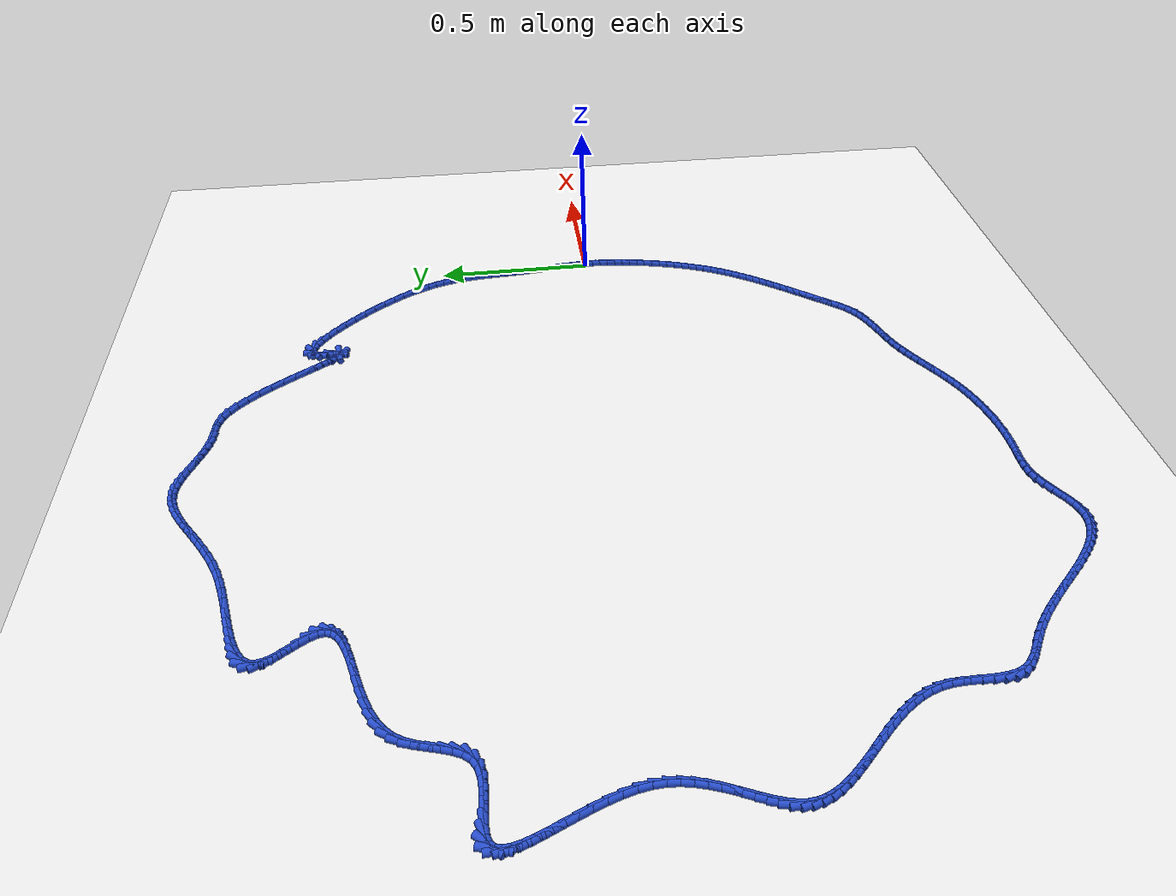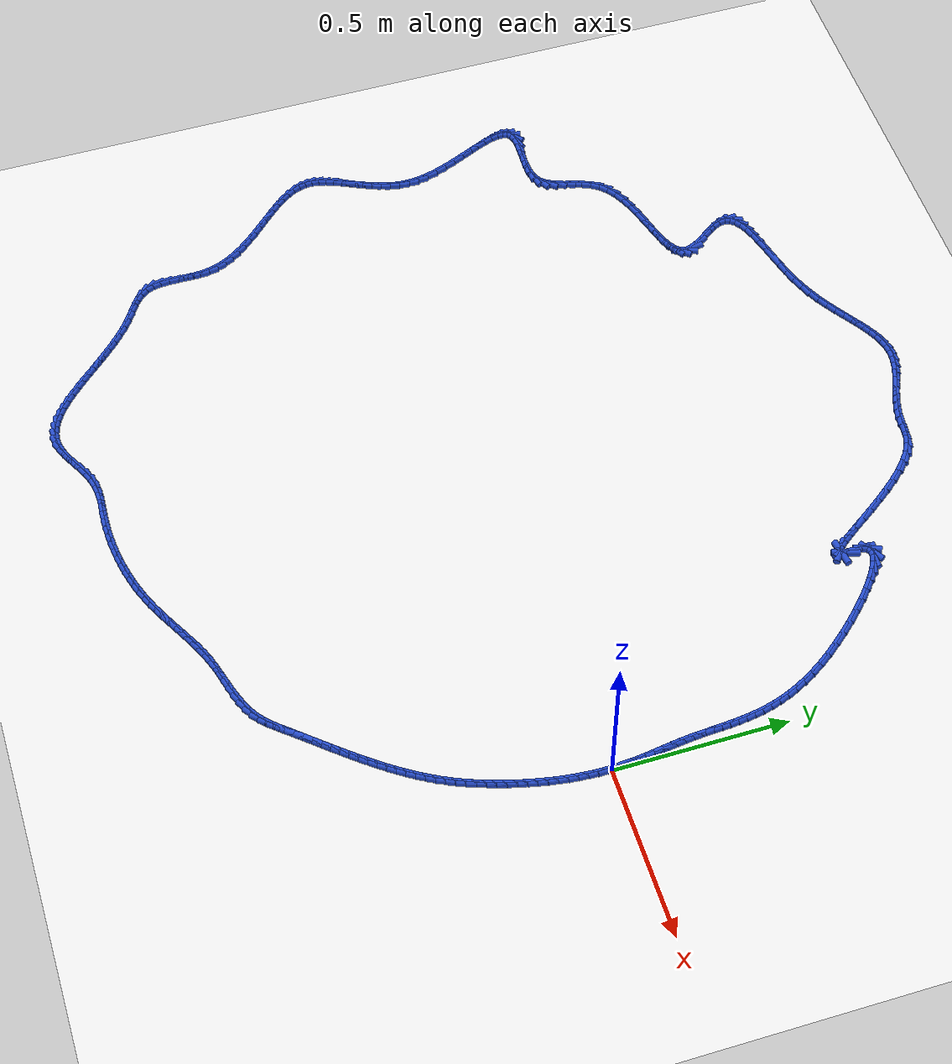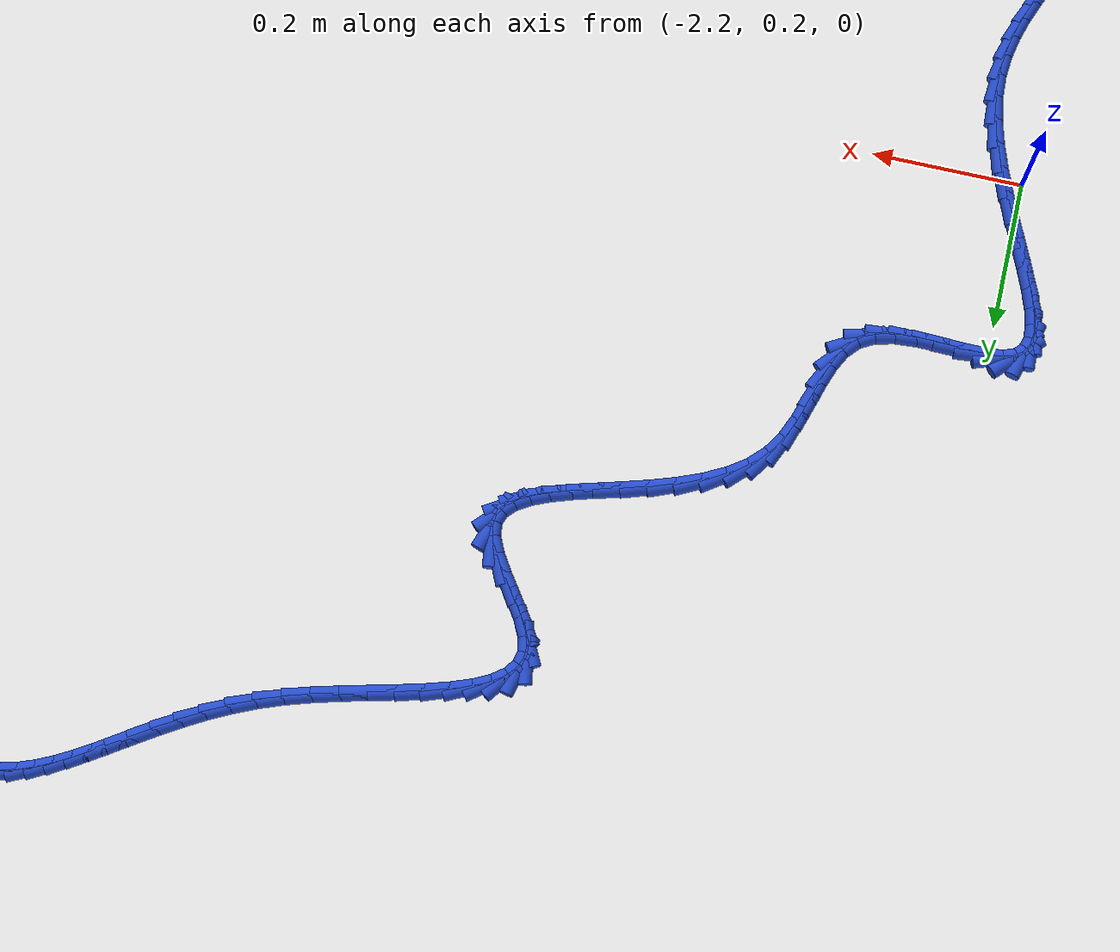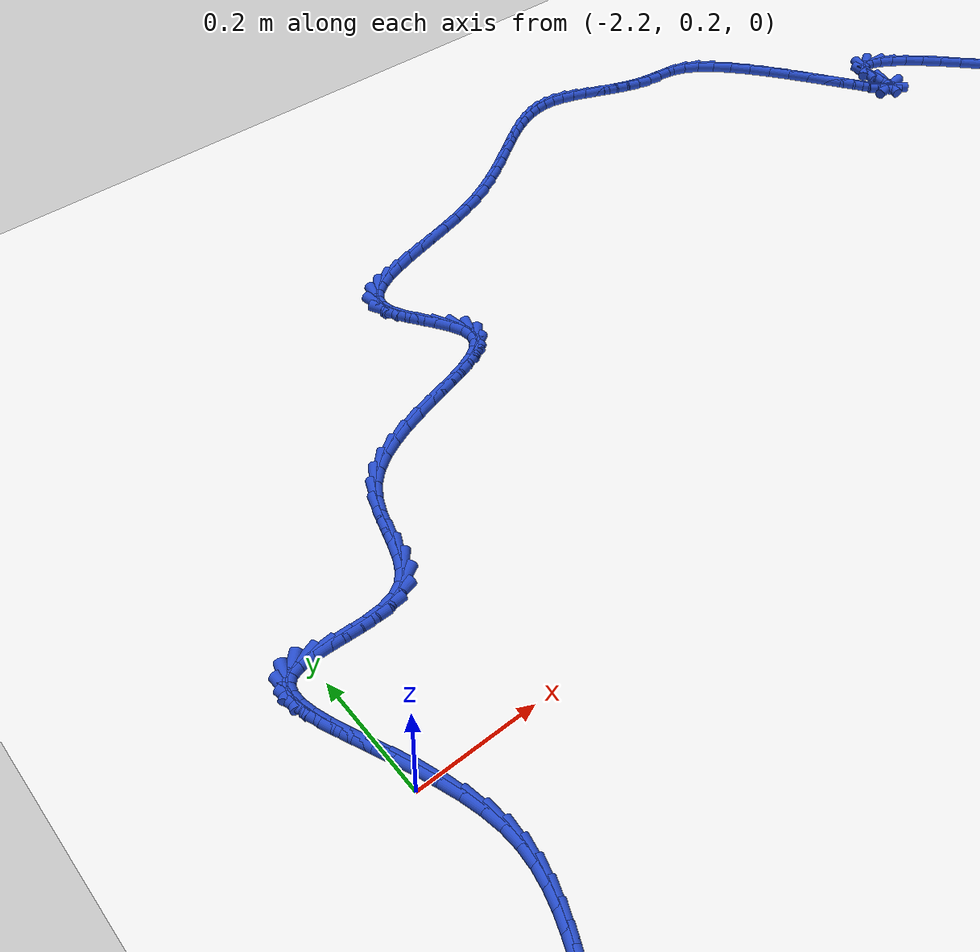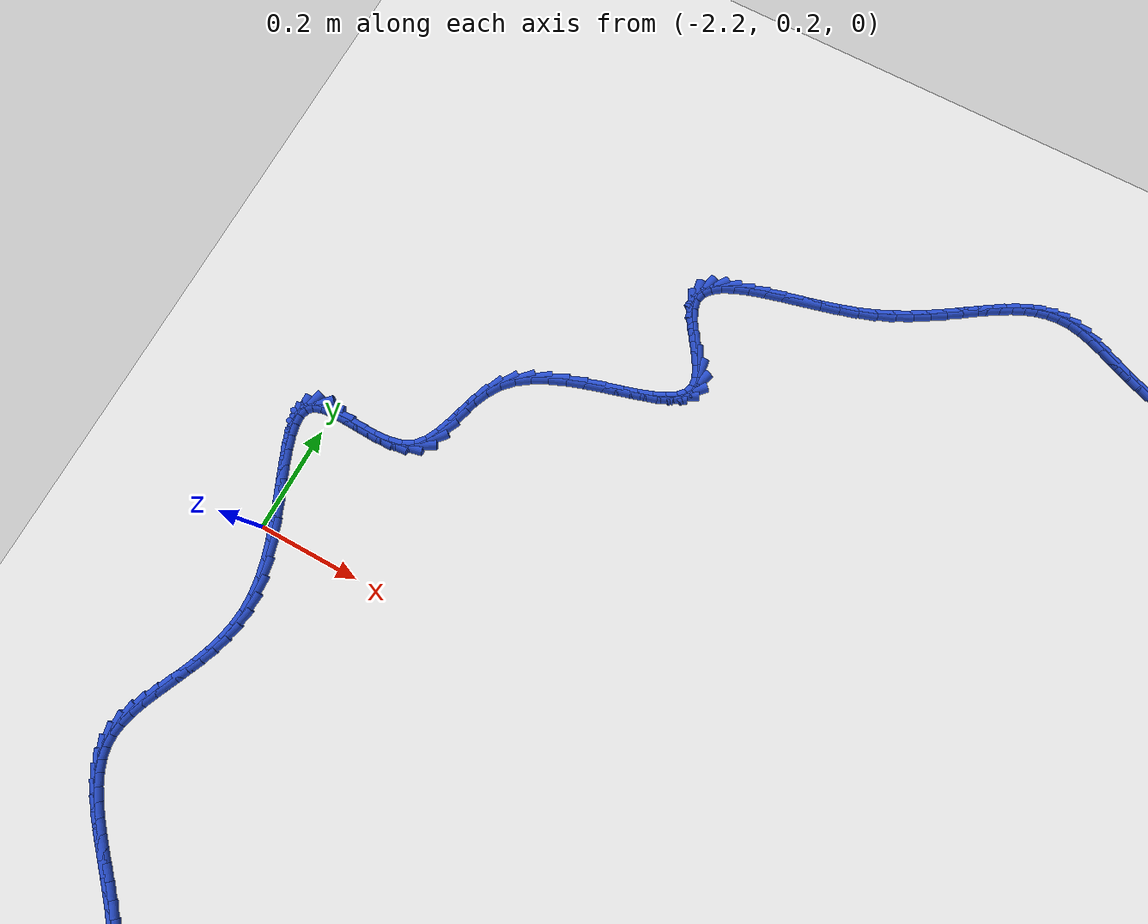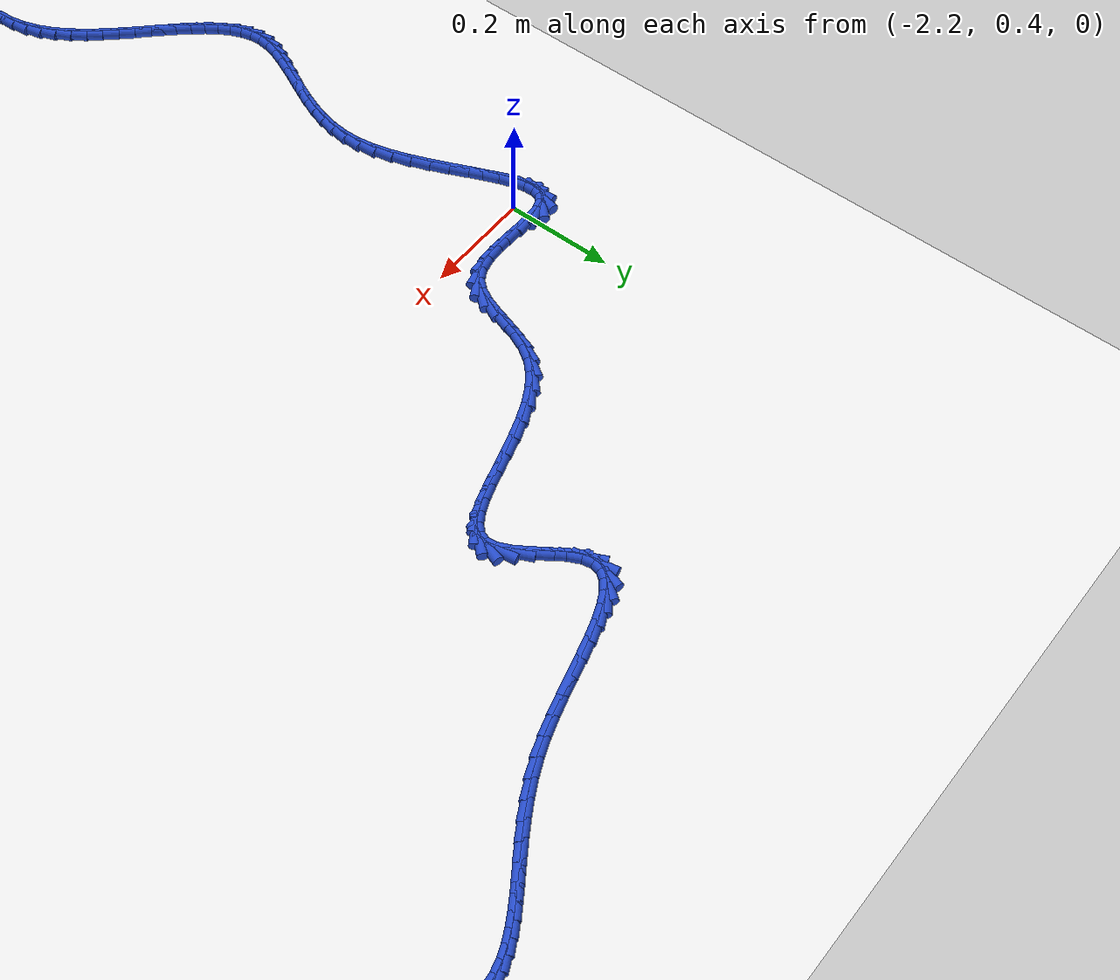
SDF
<sdf version="1.6">
 <world name="default">
  <light name="sun" type="directional">
   <pose>0 0 10 0 -0 0</pose>
   <diffuse>0.8 0.8 0.8 1</diffuse>
   <specular>0.2 0.2 0.2 1</specular>
   <attenuation>
    <range>1000</range>
    <constant>0.9</constant>
    <linear>0.01</linear>
    <quadratic>0.001</quadratic>
   </attenuation>
   <direction>-0.5 0.1 -0.9</direction>
  </light>
  <model name="ground_plane">
   <static>1</static>
   <link name="link">
    <collision name="collision">
     <geometry><plane><normal>0 0 1</normal><size>100 100</size></plane></geometry>
     <surface><friction><ode><mu>100</mu><mu2>50</mu2></ode></friction></surface>
    </collision>
    <visual name="visual">
     <cast_shadows>0</cast_shadows>
     <geometry><plane><normal>0 0 1</normal><size>100 100</size></plane></geometry>
     <material>
      <script><uri>file://media/materials/scripts/gazebo.material</uri><name>Gazebo/WhiteGlow</name></script>
     </material>
    </visual>
   </link>
  </model>
  <gravity>0 0 -9.8</gravity>
  <magnetic_field>6e-06 2.3e-05 -4.2e-05</magnetic_field>
  <atmosphere type="adiabatic"/>
  <physics name="default_physics" default="0" type="ode">
   <max_step_size>0.001</max_step_size>
   <real_time_factor>1</real_time_factor>
   <real_time_update_rate>1000</real_time_update_rate>
  </physics>
  <scene><ambient>0.4 0.4 0.4 1</ambient><background>0.7 0.7 0.7 1</background><shadows>1</shadows></scene>
  <spherical_coordinates>
   <surface_model>EARTH_WGS84</surface_model>
   <latitude_deg>0</latitude_deg>
   <longitude_deg>0</longitude_deg>
   <elevation>0</elevation>
   <heading_deg>0</heading_deg>
  </spherical_coordinates>
  <model name="line">
   <link name="link_0">
    <pose>6.071532165918825e-18 -4.85722573273506e-17 0.01 0 1.57 -1.5202687227389018</pose>
    <collision name="collision">
     <geometry><cylinder><radius>0.01</radius><length>0.08</length></cylinder></geometry>
    </collision>
    <visual name="visual">
     <material>
      <script><name>Gazebo/Blue</name><uri>file://media/materials/scripts/gazebo.material</uri></script>
     </material>
     <geometry><cylinder><radius>0.01</radius><length>0.08</length></cylinder></geometry>
    </visual>
   </link>
   <link name="link_1">
    <pose>-0.0013621839984114712 0.026936257720885662 0.01 0 1.57 -1.4878777876628857</pose>
    <collision name="collision">
     <geometry><cylinder><radius>0.01</radius><length>0.08</length></cylinder></geometry>
    </collision>
    <visual name="visual">
     <material>
      <script><name>Gazebo/Blue</name><uri>file://media/materials/scripts/gazebo.material</uri></script>
     </material>
     <geometry><cylinder><radius>0.01</radius><length>0.08</length></cylinder></geometry>
    </visual>
   </link>
   <link name="link_2">
    <pose>-0.003603920495850203 0.05390967632911264 0.01 0 1.57 -1.4630148190310512</pose>
    <collision name="collision">
     <geometry><cylinder><radius>0.01</radius><length>0.08</length></cylinder></geometry>
    </collision>
    <visual name="visual">
     <material>
      <script><name>Gazebo/Blue</name><uri>file://media/materials/scripts/gazebo.material</uri></script>
     </material>
     <geometry><cylinder><radius>0.01</radius><length>0.08</length></cylinder></geometry>
    </visual>
   </link>
   <link name="link_3">
    <pose>-0.006517943076058875 0.08084128980762992 0.01 0 1.57 -1.4454246716014492</pose>
    <collision name="collision">
     <geometry><cylinder><radius>0.01</radius><length>0.08</length></cylinder></geometry>
    </collision>
    <visual name="visual">
     <material>
      <script><name>Gazebo/Blue</name><uri>file://media/materials/scripts/gazebo.material</uri></script>
     </material>
     <geometry><cylinder><radius>0.01</radius><length>0.08</length></cylinder></geometry>
    </visual>
   </link>
   <link name="link_4">
    <pose>-0.009896985322780168 0.10765213213938638 0.01 0 1.57 -1.4349731755059414</pose>
    <collision name="collision">
     <geometry><cylinder><radius>0.01</radius><length>0.08</length></cylinder></geometry>
    </collision>
    <visual name="visual">
     <material>
      <script><name>Gazebo/Blue</name><uri>file://media/materials/scripts/gazebo.material</uri></script>
     </material>
     <geometry><cylinder><radius>0.01</radius><length>0.08</length></cylinder></geometry>
    </visual>
   </link>
   <link name="link_5">
    <pose>-0.013533780819756777 0.13426323730733108 0.01 0 1.57 -1.4316725979352658</pose>
    <collision name="collision">
     <geometry><cylinder><radius>0.01</radius><length>0.08</length></cylinder></geometry>
    </collision>
    <visual name="visual">
     <material>
      <script><name>Gazebo/Blue</name><uri>file://media/materials/scripts/gazebo.material</uri></script>
     </material>
     <geometry><cylinder><radius>0.01</radius><length>0.08</length></cylinder></geometry>
    </visual>
   </link>
   <link name="link_6">
    <pose>-0.01722106315073139 0.16059563929441306 0.01 0 1.57 -1.4357035309946928</pose>
    <collision name="collision">
     <geometry><cylinder><radius>0.01</radius><length>0.08</length></cylinder></geometry>
    </collision>
    <visual name="visual">
     <material>
      <script><name>Gazebo/Blue</name><uri>file://media/materials/scripts/gazebo.material</uri></script>
     </material>
     <geometry><cylinder><radius>0.01</radius><length>0.08</length></cylinder></geometry>
    </visual>
   </link>
   <link name="link_7">
    <pose>-0.02075156589944669 0.18657037208358124 0.01 0 1.57 -1.447436378632022</pose>
    <collision name="collision">
     <geometry><cylinder><radius>0.01</radius><length>0.08</length></cylinder></geometry>
    </collision>
    <visual name="visual">
     <material>
      <script><name>Gazebo/Blue</name><uri>file://media/materials/scripts/gazebo.material</uri></script>
     </material>
     <geometry><cylinder><radius>0.01</radius><length>0.08</length></cylinder></geometry>
    </visual>
   </link>
   <link name="link_8">
    <pose>-0.023918022649645362 0.21210846965778454 0.01 0 1.57 -1.4669296123937388</pose>
    <collision name="collision">
     <geometry><cylinder><radius>0.01</radius><length>0.08</length></cylinder></geometry>
    </collision>
    <visual name="visual">
     <material>
      <script><name>Gazebo/Blue</name><uri>file://media/materials/scripts/gazebo.material</uri></script>
     </material>
     <geometry><cylinder><radius>0.01</radius><length>0.08</length></cylinder></geometry>
    </visual>
   </link>
   <link name="link_9">
    <pose>-0.026527046002444068 0.23713702966311986 0.01 0 1.57 -1.4863525232889032</pose>
    <collision name="collision">
     <geometry><cylinder><radius>0.01</radius><length>0.08</length></cylinder></geometry>
    </collision>
    <visual name="visual">
     <material>
      <script><name>Gazebo/Blue</name><uri>file://media/materials/scripts/gazebo.material</uri></script>
     </material>
     <geometry><cylinder><radius>0.01</radius><length>0.08</length></cylinder></geometry>
    </visual>
   </link>
   <link name="link_10">
    <pose>-0.028604394348743737 0.26167889328528066 0.01 0 1.57 -1.498628566626526</pose>
    <collision name="collision">
     <geometry><cylinder><radius>0.01</radius><length>0.08</length></cylinder></geometry>
    </collision>
    <visual name="visual">
     <material>
      <script><name>Gazebo/Blue</name><uri>file://media/materials/scripts/gazebo.material</uri></script>
     </material>
     <geometry><cylinder><radius>0.01</radius><length>0.08</length></cylinder></geometry>
    </visual>
   </link>
   <link name="link_11">
    <pose>-0.030350593199935123 0.2858332564632835 0.01 0 1.57 -1.5030093183288966</pose>
    <collision name="collision">
     <geometry><cylinder><radius>0.01</radius><length>0.08</length></cylinder></geometry>
    </collision>
    <visual name="visual">
     <material>
      <script><name>Gazebo/Blue</name><uri>file://media/materials/scripts/gazebo.material</uri></script>
     </material>
     <geometry><cylinder><radius>0.01</radius><length>0.08</length></cylinder></geometry>
    </visual>
   </link>
   <link name="link_12">
    <pose>-0.0319710286408252 0.3097014386928143 0.01 0 1.57 -1.4991363128735355</pose>
    <collision name="collision">
     <geometry><cylinder><radius>0.01</radius><length>0.08</length></cylinder></geometry>
    </collision>
    <visual name="visual">
     <material>
      <script><name>Gazebo/Blue</name><uri>file://media/materials/scripts/gazebo.material</uri></script>
     </material>
     <geometry><cylinder><radius>0.01</radius><length>0.08</length></cylinder></geometry>
    </visual>
   </link>
   <link name="link_13">
    <pose>-0.03367108675622087 0.33338475946955826 0.01 0 1.57 -1.4868800694394178</pose>
    <collision name="collision">
     <geometry><cylinder><radius>0.01</radius><length>0.08</length></cylinder></geometry>
    </collision>
    <visual name="visual">
     <material>
      <script><name>Gazebo/Blue</name><uri>file://media/materials/scripts/gazebo.material</uri></script>
     </material>
     <geometry><cylinder><radius>0.01</radius><length>0.08</length></cylinder></geometry>
    </visual>
   </link>
   <link name="link_14">
    <pose>-0.03565615363092907 0.3569845382892012 0.01 0 1.57 -1.4663631767505563</pose>
    <collision name="collision">
     <geometry><cylinder><radius>0.01</radius><length>0.08</length></cylinder></geometry>
    </collision>
    <visual name="visual">
     <material>
      <script><name>Gazebo/Blue</name><uri>file://media/materials/scripts/gazebo.material</uri></script>
     </material>
     <geometry><cylinder><radius>0.01</radius><length>0.08</length></cylinder></geometry>
    </visual>
   </link>
   <link name="link_15">
    <pose>-0.038131615349756745 0.38060209464742845 0.01 0 1.57 -1.437981728939842</pose>
    <collision name="collision">
     <geometry><cylinder><radius>0.01</radius><length>0.08</length></cylinder></geometry>
    </collision>
    <visual name="visual">
     <material>
      <script><name>Gazebo/Blue</name><uri>file://media/materials/scripts/gazebo.material</uri></script>
     </material>
     <geometry><cylinder><radius>0.01</radius><length>0.08</length></cylinder></geometry>
    </visual>
   </link>
   <link name="link_16">
    <pose>-0.041302857997510836 0.4043387480399258 0.01 0 1.57 -1.402418024928704</pose>
    <collision name="collision">
     <geometry><cylinder><radius>0.01</radius><length>0.08</length></cylinder></geometry>
    </collision>
    <visual name="visual">
     <material>
      <script><name>Gazebo/Blue</name><uri>file://media/materials/scripts/gazebo.material</uri></script>
     </material>
     <geometry><cylinder><radius>0.01</radius><length>0.08</length></cylinder></geometry>
    </visual>
   </link>
   <link name="link_17">
    <pose>-0.045375267658998256 0.42829581796237853 0.01 0 1.57 -1.3606340619621375</pose>
    <collision name="collision">
     <geometry><cylinder><radius>0.01</radius><length>0.08</length></cylinder></geometry>
    </collision>
    <visual name="visual">
     <material>
      <script><name>Gazebo/Blue</name><uri>file://media/materials/scripts/gazebo.material</uri></script>
     </material>
     <geometry><cylinder><radius>0.01</radius><length>0.08</length></cylinder></geometry>
    </visual>
   </link>
   <link name="link_18">
    <pose>-0.05055423041902593 0.45257462391047243 0.01 0 1.57 -1.313835653054999</pose>
    <collision name="collision">
     <geometry><cylinder><radius>0.01</radius><length>0.08</length></cylinder></geometry>
    </collision>
    <visual name="visual">
     <material>
      <script><name>Gazebo/Blue</name><uri>file://media/materials/scripts/gazebo.material</uri></script>
     </material>
     <geometry><cylinder><radius>0.01</radius><length>0.08</length></cylinder></geometry>
    </visual>
   </link>
   <link name="link_19">
    <pose>-0.05704513236240083 0.4772764853798929 0.01 0 1.57 -1.2634025208370234</pose>
    <collision name="collision">
     <geometry><cylinder><radius>0.01</radius><length>0.08</length></cylinder></geometry>
    </collision>
    <visual name="visual">
     <material>
      <script><name>Gazebo/Blue</name><uri>file://media/materials/scripts/gazebo.material</uri></script>
     </material>
     <geometry><cylinder><radius>0.01</radius><length>0.08</length></cylinder></geometry>
    </visual>
   </link>
   <link name="link_20">
    <pose>-0.06505335957392987 0.5025027218663257 0.01 0 1.57 -1.2107896177288502</pose>
    <collision name="collision">
     <geometry><cylinder><radius>0.01</radius><length>0.08</length></cylinder></geometry>
    </collision>
    <visual name="visual">
     <material>
      <script><name>Gazebo/Blue</name><uri>file://media/materials/scripts/gazebo.material</uri></script>
     </material>
     <geometry><cylinder><radius>0.01</radius><length>0.08</length></cylinder></geometry>
    </visual>
   </link>
   <link name="link_21">
    <pose>-0.07478429813841997 0.5283546528654562 0.01 0 1.57 -1.1574153115900203</pose>
    <collision name="collision">
     <geometry><cylinder><radius>0.01</radius><length>0.08</length></cylinder></geometry>
    </collision>
    <visual name="visual">
     <material>
      <script><name>Gazebo/Blue</name><uri>file://media/materials/scripts/gazebo.material</uri></script>
     </material>
     <geometry><cylinder><radius>0.01</radius><length>0.08</length></cylinder></geometry>
    </visual>
   </link>
   <link name="link_22">
    <pose>-0.0864433341406781 0.5549335978729701 0.01 0 1.57 -1.1045577293823192</pose>
    <collision name="collision">
     <geometry><cylinder><radius>0.01</radius><length>0.08</length></cylinder></geometry>
    </collision>
    <visual name="visual">
     <material>
      <script><name>Gazebo/Blue</name><uri>file://media/materials/scripts/gazebo.material</uri></script>
     </material>
     <geometry><cylinder><radius>0.01</radius><length>0.08</length></cylinder></geometry>
    </visual>
   </link>
   <link name="link_23">
    <pose>-0.10023585366551116 0.5823408763845528 0.01 0 1.57 -1.0532783132168577</pose>
    <collision name="collision">
     <geometry><cylinder><radius>0.01</radius><length>0.08</length></cylinder></geometry>
    </collision>
    <visual name="visual">
     <material>
      <script><name>Gazebo/Blue</name><uri>file://media/materials/scripts/gazebo.material</uri></script>
     </material>
     <geometry><cylinder><radius>0.01</radius><length>0.08</length></cylinder></geometry>
    </visual>
   </link>
   <link name="link_24">
    <pose>-0.11636724279772609 0.6106778078958899 0.01 0 1.57 -1.004382760230723</pose>
    <collision name="collision">
     <geometry><cylinder><radius>0.01</radius><length>0.08</length></cylinder></geometry>
    </collision>
    <visual name="visual">
     <material>
      <script><name>Gazebo/Blue</name><uri>file://media/materials/scripts/gazebo.material</uri></script>
     </material>
     <geometry><cylinder><radius>0.01</radius><length>0.08</length></cylinder></geometry>
    </visual>
   </link>
   <link name="link_25">
    <pose>-0.13504288762212985 0.640045711902667 0.01 0 1.57 -0.9584186523242824</pose>
    <collision name="collision">
     <geometry><cylinder><radius>0.01</radius><length>0.08</length></cylinder></geometry>
    </collision>
    <visual name="visual">
     <material>
      <script><name>Gazebo/Blue</name><uri>file://media/materials/scripts/gazebo.material</uri></script>
     </material>
     <geometry><cylinder><radius>0.01</radius><length>0.08</length></cylinder></geometry>
    </visual>
   </link>
   <link name="link_26">
    <pose>-0.15646817422352932 0.6705459079005696 0.01 0 1.57 -0.9161712435235088</pose>
    <collision name="collision">
     <geometry><cylinder><radius>0.01</radius><length>0.08</length></cylinder></geometry>
    </collision>
    <visual name="visual">
     <material>
      <script><name>Gazebo/Blue</name><uri>file://media/materials/scripts/gazebo.material</uri></script>
     </material>
     <geometry><cylinder><radius>0.01</radius><length>0.08</length></cylinder></geometry>
    </visual>
   </link>
   <link name="link_27">
    <pose>-0.1807449769752361 0.702175760316052 0.01 0 1.57 -0.8790830635248844</pose>
    <collision name="collision">
     <geometry><cylinder><radius>0.01</radius><length>0.08</length></cylinder></geometry>
    </collision>
    <visual name="visual">
     <material>
      <script><name>Gazebo/Blue</name><uri>file://media/materials/scripts/gazebo.material</uri></script>
     </material>
     <geometry><cylinder><radius>0.01</radius><length>0.08</length></cylinder></geometry>
    </visual>
   </link>
   <link name="link_28">
    <pose>-0.20737909109445912 0.7343340013141078 0.01 0 1.57 -0.844959928777115</pose>
    <collision name="collision">
     <geometry><cylinder><radius>0.01</radius><length>0.08</length></cylinder></geometry>
    </collision>
    <visual name="visual">
     <material>
      <script><name>Gazebo/Blue</name><uri>file://media/materials/scripts/gazebo.material</uri></script>
     </material>
     <geometry><cylinder><radius>0.01</radius><length>0.08</length></cylinder></geometry>
    </visual>
   </link>
   <link name="link_29">
    <pose>-0.23566337948588661 0.7662055187229899 0.01 0 1.57 -0.8110999288396866</pose>
    <collision name="collision">
     <geometry><cylinder><radius>0.01</radius><length>0.08</length></cylinder></geometry>
    </collision>
    <visual name="visual">
     <material>
      <script><name>Gazebo/Blue</name><uri>file://media/materials/scripts/gazebo.material</uri></script>
     </material>
     <geometry><cylinder><radius>0.01</radius><length>0.08</length></cylinder></geometry>
    </visual>
   </link>
   <link name="link_30">
    <pose>-0.2648904391519137 0.7969749333297543 0.01 0 1.57 -0.7749295062159781</pose>
    <collision name="collision">
     <geometry><cylinder><radius>0.01</radius><length>0.08</length></cylinder></geometry>
    </collision>
    <visual name="visual">
     <material>
      <script><name>Gazebo/Blue</name><uri>file://media/materials/scripts/gazebo.material</uri></script>
     </material>
     <geometry><cylinder><radius>0.01</radius><length>0.08</length></cylinder></geometry>
    </visual>
   </link>
   <link name="link_31">
    <pose>-0.29435286709493536 0.8258268659214568 0.01 0 1.57 -0.7333430779876376</pose>
    <collision name="collision">
     <geometry><cylinder><radius>0.01</radius><length>0.08</length></cylinder></geometry>
    </collision>
    <visual name="visual">
     <material>
      <script><name>Gazebo/Blue</name><uri>file://media/materials/scripts/gazebo.material</uri></script>
     </material>
     <geometry><cylinder><radius>0.01</radius><length>0.08</length></cylinder></geometry>
    </visual>
   </link>
   <link name="link_32">
    <pose>-0.323343260317347 0.8519459372851538 0.01 0 1.57 -0.6817624799625955</pose>
    <collision name="collision">
     <geometry><cylinder><radius>0.01</radius><length>0.08</length></cylinder></geometry>
    </collision>
    <visual name="visual">
     <material>
      <script><name>Gazebo/Blue</name><uri>file://media/materials/scripts/gazebo.material</uri></script>
     </material>
     <geometry><cylinder><radius>0.01</radius><length>0.08</length></cylinder></geometry>
    </visual>
   </link>
   <link name="link_33">
    <pose>-0.35115421582154355 0.8745167682079008 0.01 0 1.57 -0.6122861447464318</pose>
    <collision name="collision">
     <geometry><cylinder><radius>0.01</radius><length>0.08</length></cylinder></geometry>
    </collision>
    <visual name="visual">
     <material>
      <script><name>Gazebo/Blue</name><uri>file://media/materials/scripts/gazebo.material</uri></script>
     </material>
     <geometry><cylinder><radius>0.01</radius><length>0.08</length></cylinder></geometry>
    </visual>
   </link>
   <link name="link_34">
    <pose>-0.3770783306099204 0.8927239794767546 0.01 0 1.57 -0.5092960089770318</pose>
    <collision name="collision">
     <geometry><cylinder><radius>0.01</radius><length>0.08</length></cylinder></geometry>
    </collision>
    <visual name="visual">
     <material>
      <script><name>Gazebo/Blue</name><uri>file://media/materials/scripts/gazebo.material</uri></script>
     </material>
     <geometry><cylinder><radius>0.01</radius><length>0.08</length></cylinder></geometry>
    </visual>
   </link>
   <link name="link_35">
    <pose>-0.4004082016848725 0.905752191878771 0.01 0 1.57 -0.33773999124530535</pose>
    <collision name="collision">
     <geometry><cylinder><radius>0.01</radius><length>0.08</length></cylinder></geometry>
    </collision>
    <visual name="visual">
     <material>
      <script><name>Gazebo/Blue</name><uri>file://media/materials/scripts/gazebo.material</uri></script>
     </material>
     <geometry><cylinder><radius>0.01</radius><length>0.08</length></cylinder></geometry>
    </visual>
   </link>
   <link name="link_36">
    <pose>-0.42043642604879505 0.9127860262010059 0.01 0 1.57 -0.013987138621494057</pose>
    <collision name="collision">
     <geometry><cylinder><radius>0.01</radius><length>0.08</length></cylinder></geometry>
    </collision>
    <visual name="visual">
     <material>
      <script><name>Gazebo/Blue</name><uri>file://media/materials/scripts/gazebo.material</uri></script>
     </material>
     <geometry><cylinder><radius>0.01</radius><length>0.08</length></cylinder></geometry>
    </visual>
   </link>
   <link name="link_37">
    <pose>-0.4364556007040834 0.9130101032305155 0.01 0 1.57 0.5797444640844538</pose>
    <collision name="collision">
     <geometry><cylinder><radius>0.01</radius><length>0.08</length></cylinder></geometry>
    </collision>
    <visual name="visual">
     <material>
      <script><name>Gazebo/Blue</name><uri>file://media/materials/scripts/gazebo.material</uri></script>
     </material>
     <geometry><cylinder><radius>0.01</radius><length>0.08</length></cylinder></geometry>
    </visual>
   </link>
   <link name="link_38">
    <pose>-0.4477583226531323 0.9056090437543557 0.01 0 1.57 1.2154460100073714</pose>
    <collision name="collision">
     <geometry><cylinder><radius>0.01</radius><length>0.08</length></cylinder></geometry>
    </collision>
    <visual name="visual">
     <material>
      <script><name>Gazebo/Blue</name><uri>file://media/materials/scripts/gazebo.material</uri></script>
     </material>
     <geometry><cylinder><radius>0.01</radius><length>0.08</length></cylinder></geometry>
    </visual>
   </link>
   <link name="link_39">
    <pose>-0.45363718889833726 0.8897674685595827 0.01 0 1.57 -1.5693667749853224</pose>
    <collision name="collision">
     <geometry><cylinder><radius>0.01</radius><length>0.08</length></cylinder></geometry>
    </collision>
    <visual name="visual">
     <material>
      <script><name>Gazebo/Blue</name><uri>file://media/materials/scripts/gazebo.material</uri></script>
     </material>
     <geometry><cylinder><radius>0.01</radius><length>0.08</length></cylinder></geometry>
    </visual>
   </link>
   <link name="link_40">
    <pose>-0.45360193034756197 0.865103425940899 0.01 0 1.57 -1.5482742946269215</pose>
    <collision name="collision">
     <geometry><cylinder><radius>0.01</radius><length>0.08</length></cylinder></geometry>
    </collision>
    <visual name="visual">
     <material>
      <script><name>Gazebo/Blue</name><uri>file://media/materials/scripts/gazebo.material</uri></script>
     </material>
     <geometry><cylinder><radius>0.01</radius><length>0.08</length></cylinder></geometry>
    </visual>
   </link>
   <link name="link_41">
    <pose>-0.453104415607279 0.843017025672246 0.01 0 1.57 1.2708311615728876</pose>
    <collision name="collision">
     <geometry><cylinder><radius>0.01</radius><length>0.08</length></cylinder></geometry>
    </collision>
    <visual name="visual">
     <material>
      <script><name>Gazebo/Blue</name><uri>file://media/materials/scripts/gazebo.material</uri></script>
     </material>
     <geometry><cylinder><radius>0.01</radius><length>0.08</length></cylinder></geometry>
    </visual>
   </link>
   <link name="link_42">
    <pose>-0.4565120910640011 0.8319995779230078 0.01 0 1.57 0.15256588074858432</pose>
    <collision name="collision">
     <geometry><cylinder><radius>0.01</radius><length>0.08</length></cylinder></geometry>
    </collision>
    <visual name="visual">
     <material>
      <script><name>Gazebo/Blue</name><uri>file://media/materials/scripts/gazebo.material</uri></script>
     </material>
     <geometry><cylinder><radius>0.01</radius><length>0.08</length></cylinder></geometry>
    </visual>
   </link>
   <link name="link_43">
    <pose>-0.4635730264974117 0.8309138833207236 0.01 0 1.57 -0.630652644858088</pose>
    <collision name="collision">
     <geometry><cylinder><radius>0.01</radius><length>0.08</length></cylinder></geometry>
    </collision>
    <visual name="visual">
     <material>
      <script><name>Gazebo/Blue</name><uri>file://media/materials/scripts/gazebo.material</uri></script>
     </material>
     <geometry><cylinder><radius>0.01</radius><length>0.08</length></cylinder></geometry>
    </visual>
   </link>
   <link name="link_44">
    <pose>-0.4739831339903845 0.838514456887011 0.01 0 1.57 -0.8410024436571727</pose>
    <collision name="collision">
     <geometry><cylinder><radius>0.01</radius><length>0.08</length></cylinder></geometry>
    </collision>
    <visual name="visual">
     <material>
      <script><name>Gazebo/Blue</name><uri>file://media/materials/scripts/gazebo.material</uri></script>
     </material>
     <geometry><cylinder><radius>0.01</radius><length>0.08</length></cylinder></geometry>
    </visual>
   </link>
   <link name="link_45">
    <pose>-0.48743832562579387 0.8535558136434883 0.01 0 1.57 -0.9192466775177843</pose>
    <collision name="collision">
     <geometry><cylinder><radius>0.01</radius><length>0.08</length></cylinder></geometry>
    </collision>
    <visual name="visual">
     <material>
      <script><name>Gazebo/Blue</name><uri>file://media/materials/scripts/gazebo.material</uri></script>
     </material>
     <geometry><cylinder><radius>0.01</radius><length>0.08</length></cylinder></geometry>
    </visual>
   </link>
   <link name="link_46">
    <pose>-0.5036345134865138 0.874792468611774 0.01 0 1.57 -0.9523577638987667</pose>
    <collision name="collision">
     <geometry><cylinder><radius>0.01</radius><length>0.08</length></cylinder></geometry>
    </collision>
    <visual name="visual">
     <material>
      <script><name>Gazebo/Blue</name><uri>file://media/materials/scripts/gazebo.material</uri></script>
     </material>
     <geometry><cylinder><radius>0.01</radius><length>0.08</length></cylinder></geometry>
    </visual>
   </link>
   <link name="link_47">
    <pose>-0.522267609655418 0.900978936813485 0.01 0 1.57 -0.963618666770061</pose>
    <collision name="collision">
     <geometry><cylinder><radius>0.01</radius><length>0.08</length></cylinder></geometry>
    </collision>
    <visual name="visual">
     <material>
      <script><name>Gazebo/Blue</name><uri>file://media/materials/scripts/gazebo.material</uri></script>
     </material>
     <geometry><cylinder><radius>0.01</radius><length>0.08</length></cylinder></geometry>
    </visual>
   </link>
   <link name="link_48">
    <pose>-0.5430335262153811 0.9308697332702403 0.01 0 1.57 -0.9611104917837557</pose>
    <collision name="collision">
     <geometry><cylinder><radius>0.01</radius><length>0.08</length></cylinder></geometry>
    </collision>
    <visual name="visual">
     <material>
      <script><name>Gazebo/Blue</name><uri>file://media/materials/scripts/gazebo.material</uri></script>
     </material>
     <geometry><cylinder><radius>0.01</radius><length>0.08</length></cylinder></geometry>
    </visual>
   </link>
   <link name="link_49">
    <pose>-0.5656281752492764 0.9632193730036571 0.01 0 1.57 -0.9476777698730287</pose>
    <collision name="collision">
     <geometry><cylinder><radius>0.01</radius><length>0.08</length></cylinder></geometry>
    </collision>
    <visual name="visual">
     <material>
      <script><name>Gazebo/Blue</name><uri>file://media/materials/scripts/gazebo.material</uri></script>
     </material>
     <geometry><cylinder><radius>0.01</radius><length>0.08</length></cylinder></geometry>
    </visual>
   </link>
   <link name="link_50">
    <pose>-0.5897474688399786 0.9967823710353542 0.01 0 1.57 -0.9236463535046997</pose>
    <collision name="collision">
     <geometry><cylinder><radius>0.01</radius><length>0.08</length></cylinder></geometry>
    </collision>
    <visual name="visual">
     <material>
      <script><name>Gazebo/Blue</name><uri>file://media/materials/scripts/gazebo.material</uri></script>
     </material>
     <geometry><cylinder><radius>0.01</radius><length>0.08</length></cylinder></geometry>
    </visual>
   </link>
   <link name="link_51">
    <pose>-0.6150873190703615 1.030313242386949 0.01 0 1.57 -0.8875365227898391</pose>
    <collision name="collision">
     <geometry><cylinder><radius>0.01</radius><length>0.08</length></cylinder></geometry>
    </collision>
    <visual name="visual">
     <material>
      <script><name>Gazebo/Blue</name><uri>file://media/materials/scripts/gazebo.material</uri></script>
     </material>
     <geometry><cylinder><radius>0.01</radius><length>0.08</length></cylinder></geometry>
    </visual>
   </link>
   <link name="link_52">
    <pose>-0.6413436380232991 1.06256650208006 0.01 0 1.57 -0.8359120592686451</pose>
    <collision name="collision">
     <geometry><cylinder><radius>0.01</radius><length>0.08</length></cylinder></geometry>
    </collision>
    <visual name="visual">
     <material>
      <script><name>Gazebo/Blue</name><uri>file://media/materials/scripts/gazebo.material</uri></script>
     </material>
     <geometry><cylinder><radius>0.01</radius><length>0.08</length></cylinder></geometry>
    </visual>
   </link>
   <link name="link_53">
    <pose>-0.6682123377816653 1.0922966651363046 0.01 0 1.57 -0.7625296663524496</pose>
    <collision name="collision">
     <geometry><cylinder><radius>0.01</radius><length>0.08</length></cylinder></geometry>
    </collision>
    <visual name="visual">
     <material>
      <script><name>Gazebo/Blue</name><uri>file://media/materials/scripts/gazebo.material</uri></script>
     </material>
     <geometry><cylinder><radius>0.01</radius><length>0.08</length></cylinder></geometry>
    </visual>
   </link>
   <link name="link_54">
    <pose>-0.6953893304283343 1.118258246577301 0.01 0 1.57 -0.6565941498748069</pose>
    <collision name="collision">
     <geometry><cylinder><radius>0.01</radius><length>0.08</length></cylinder></geometry>
    </collision>
    <visual name="visual">
     <material>
      <script><name>Gazebo/Blue</name><uri>file://media/materials/scripts/gazebo.material</uri></script>
     </material>
     <geometry><cylinder><radius>0.01</radius><length>0.08</length></cylinder></geometry>
    </visual>
   </link>
   <link name="link_55">
    <pose>-0.7225705280461803 1.1392057614246676 0.01 0 1.57 -0.5003534145019489</pose>
    <collision name="collision">
     <geometry><cylinder><radius>0.01</radius><length>0.08</length></cylinder></geometry>
    </collision>
    <visual name="visual">
     <material>
      <script><name>Gazebo/Blue</name><uri>file://media/materials/scripts/gazebo.material</uri></script>
     </material>
     <geometry><cylinder><radius>0.01</radius><length>0.08</length></cylinder></geometry>
    </visual>
   </link>
   <link name="link_56">
    <pose>-0.7494531698438683 1.1539041541249444 0.01 0 1.57 -0.3071795195601997</pose>
    <collision name="collision">
     <geometry><cylinder><radius>0.01</radius><length>0.08</length></cylinder></geometry>
    </collision>
    <visual name="visual">
     <material>
      <script><name>Gazebo/Blue</name><uri>file://media/materials/scripts/gazebo.material</uri></script>
     </material>
     <geometry><cylinder><radius>0.01</radius><length>0.08</length></cylinder></geometry>
    </visual>
   </link>
   <link name="link_57">
    <pose>-0.7758833735669134 1.1622883543159543 0.01 0 1.57 -0.16060609550666471</pose>
    <collision name="collision">
     <geometry><cylinder><radius>0.01</radius><length>0.08</length></cylinder></geometry>
    </collision>
    <visual name="visual">
     <material>
      <script><name>Gazebo/Blue</name><uri>file://media/materials/scripts/gazebo.material</uri></script>
     </material>
     <geometry><cylinder><radius>0.01</radius><length>0.08</length></cylinder></geometry>
    </visual>
   </link>
   <link name="link_58">
    <pose>-0.8019903108506162 1.1665177147551369 0.01 0 1.57 -0.0954093837573896</pose>
    <collision name="collision">
     <geometry><cylinder><radius>0.01</radius><length>0.08</length></cylinder></geometry>
    </collision>
    <visual name="visual">
     <material>
      <script><name>Gazebo/Blue</name><uri>file://media/materials/scripts/gazebo.material</uri></script>
     </material>
     <geometry><cylinder><radius>0.01</radius><length>0.08</length></cylinder></geometry>
    </visual>
   </link>
   <link name="link_59">
    <pose>-0.8279348402460798 1.1690006047676011 0.01 0 1.57 -0.12063070650166288</pose>
    <collision name="collision">
     <geometry><cylinder><radius>0.01</radius><length>0.08</length></cylinder></geometry>
    </collision>
    <visual name="visual">
     <material>
      <script><name>Gazebo/Blue</name><uri>file://media/materials/scripts/gazebo.material</uri></script>
     </material>
     <geometry><cylinder><radius>0.01</radius><length>0.08</length></cylinder></geometry>
    </visual>
   </link>
   <link name="link_60">
    <pose>-0.8538778203044062 1.1721453936784543 0.01 0 1.57 -0.21832715857526336</pose>
    <collision name="collision">
     <geometry><cylinder><radius>0.01</radius><length>0.08</length></cylinder></geometry>
    </collision>
    <visual name="visual">
     <material>
      <script><name>Gazebo/Blue</name><uri>file://media/materials/scripts/gazebo.material</uri></script>
     </material>
     <geometry><cylinder><radius>0.01</radius><length>0.08</length></cylinder></geometry>
    </visual>
   </link>
   <link name="link_61">
    <pose>-0.8799413938124724 1.177927951502651 0.01 0 1.57 -0.30485944899552486</pose>
    <collision name="collision">
     <geometry><cylinder><radius>0.01</radius><length>0.08</length></cylinder></geometry>
    </collision>
    <visual name="visual">
     <material>
      <script><name>Gazebo/Blue</name><uri>file://media/materials/scripts/gazebo.material</uri></script>
     </material>
     <geometry><cylinder><radius>0.01</radius><length>0.08</length></cylinder></geometry>
    </visual>
   </link>
   <link name="link_62">
    <pose>-0.906052573610294 1.1861443238581844 0.01 0 1.57 -0.35883309516860484</pose>
    <collision name="collision">
     <geometry><cylinder><radius>0.01</radius><length>0.08</length></cylinder></geometry>
    </collision>
    <visual name="visual">
     <material>
      <script><name>Gazebo/Blue</name><uri>file://media/materials/scripts/gazebo.material</uri></script>
     </material>
     <geometry><cylinder><radius>0.01</radius><length>0.08</length></cylinder></geometry>
    </visual>
   </link>
   <link name="link_63">
    <pose>-0.9320770353660446 1.195905350090115 0.01 0 1.57 -0.3836732709522244</pose>
    <collision name="collision">
     <geometry><cylinder><radius>0.01</radius><length>0.08</length></cylinder></geometry>
    </collision>
    <visual name="visual">
     <material>
      <script><name>Gazebo/Blue</name><uri>file://media/materials/scripts/gazebo.material</uri></script>
     </material>
     <geometry><cylinder><radius>0.01</radius><length>0.08</length></cylinder></geometry>
    </visual>
   </link>
   <link name="link_64">
    <pose>-0.9578804324777763 1.206321620760834 0.01 0 1.57 -0.3806049964861435</pose>
    <collision name="collision">
     <geometry><cylinder><radius>0.01</radius><length>0.08</length></cylinder></geometry>
    </collision>
    <visual name="visual">
     <material>
      <script><name>Gazebo/Blue</name><uri>file://media/materials/scripts/gazebo.material</uri></script>
     </material>
     <geometry><cylinder><radius>0.01</radius><length>0.08</length></cylinder></geometry>
    </visual>
   </link>
   <link name="link_65">
    <pose>-0.9833284183435432 1.2165037264327343 0.01 0 1.57 -0.34816262555777616</pose>
    <collision name="collision">
     <geometry><cylinder><radius>0.01</radius><length>0.08</length></cylinder></geometry>
    </collision>
    <visual name="visual">
     <material>
      <script><name>Gazebo/Blue</name><uri>file://media/materials/scripts/gazebo.material</uri></script>
     </material>
     <geometry><cylinder><radius>0.01</radius><length>0.08</length></cylinder></geometry>
    </visual>
   </link>
   <link name="link_66">
    <pose>-1.0082866463613998 1.2255622576682088 0.01 0 1.57 -0.28182718618476227</pose>
    <collision name="collision">
     <geometry><cylinder><radius>0.01</radius><length>0.08</length></cylinder></geometry>
    </collision>
    <visual name="visual">
     <material>
      <script><name>Gazebo/Blue</name><uri>file://media/materials/scripts/gazebo.material</uri></script>
     </material>
     <geometry><cylinder><radius>0.01</radius><length>0.08</length></cylinder></geometry>
    </visual>
   </link>
   <link name="link_67">
    <pose>-1.0326207699293979 1.2326078050296492 0.01 0 1.57 -0.17398242949517562</pose>
    <collision name="collision">
     <geometry><cylinder><radius>0.01</radius><length>0.08</length></cylinder></geometry>
    </collision>
    <visual name="visual">
     <material>
      <script><name>Gazebo/Blue</name><uri>file://media/materials/scripts/gazebo.material</uri></script>
     </material>
     <geometry><cylinder><radius>0.01</radius><length>0.08</length></cylinder></geometry>
    </visual>
   </link>
   <link name="link_68">
    <pose>-1.0561965825019235 1.23675147627866 0.01 0 1.57 -0.028811212141371677</pose>
    <collision name="collision">
     <geometry><cylinder><radius>0.01</radius><length>0.08</length></cylinder></geometry>
    </collision>
    <visual name="visual">
     <material>
      <script><name>Gazebo/Blue</name><uri>file://media/materials/scripts/gazebo.material</uri></script>
     </material>
     <geometry><cylinder><radius>0.01</radius><length>0.08</length></cylinder></geometry>
    </visual>
   </link>
   <link name="link_69">
    <pose>-1.0789619772237475 1.2374075564398261 0.01 0 1.57 0.11718021869951584</pose>
    <collision name="collision">
     <geometry><cylinder><radius>0.01</radius><length>0.08</length></cylinder></geometry>
    </collision>
    <visual name="visual">
     <material>
      <script><name>Gazebo/Blue</name><uri>file://media/materials/scripts/gazebo.material</uri></script>
     </material>
     <geometry><cylinder><radius>0.01</radius><length>0.08</length></cylinder></geometry>
    </visual>
   </link>
   <link name="link_70">
    <pose>-1.1010849830401146 1.2348032467516248 0.01 0 1.57 0.24850769849406085</pose>
    <collision name="collision">
     <geometry><cylinder><radius>0.01</radius><length>0.08</length></cylinder></geometry>
    </collision>
    <visual name="visual">
     <material>
      <script><name>Gazebo/Blue</name><uri>file://media/materials/scripts/gazebo.material</uri></script>
     </material>
     <geometry><cylinder><radius>0.01</radius><length>0.08</length></cylinder></geometry>
    </visual>
   </link>
   <link name="link_71">
    <pose>-1.1227701395593976 1.229300574818688 0.01 0 1.57 0.35854848916392595</pose>
    <collision name="collision">
     <geometry><cylinder><radius>0.01</radius><length>0.08</length></cylinder></geometry>
    </collision>
    <visual name="visual">
     <material>
      <script><name>Gazebo/Blue</name><uri>file://media/materials/scripts/gazebo.material</uri></script>
     </material>
     <geometry><cylinder><radius>0.01</radius><length>0.08</length></cylinder></geometry>
    </visual>
   </link>
   <link name="link_72">
    <pose>-1.1442219863899705 1.2212615682456474 0.01 0 1.57 0.44486995312543687</pose>
    <collision name="collision">
     <geometry><cylinder><radius>0.01</radius><length>0.08</length></cylinder></geometry>
    </collision>
    <visual name="visual">
     <material>
      <script><name>Gazebo/Blue</name><uri>file://media/materials/scripts/gazebo.material</uri></script>
     </material>
     <geometry><cylinder><radius>0.01</radius><length>0.08</length></cylinder></geometry>
    </visual>
   </link>
   <link name="link_73">
    <pose>-1.1656450631402069 1.2110482546371346 0.01 0 1.57 0.5080261648451341</pose>
    <collision name="collision">
     <geometry><cylinder><radius>0.01</radius><length>0.08</length></cylinder></geometry>
    </collision>
    <visual name="visual">
     <material>
      <script><name>Gazebo/Blue</name><uri>file://media/materials/scripts/gazebo.material</uri></script>
     </material>
     <geometry><cylinder><radius>0.01</radius><length>0.08</length></cylinder></geometry>
    </visual>
   </link>
   <link name="link_74">
    <pose>-1.18724390941848 1.1990226615977815 0.01 0 1.57 0.5500102541060132</pose>
    <collision name="collision">
     <geometry><cylinder><radius>0.01</radius><length>0.08</length></cylinder></geometry>
    </collision>
    <visual name="visual">
     <material>
      <script><name>Gazebo/Blue</name><uri>file://media/materials/scripts/gazebo.material</uri></script>
     </material>
     <geometry><cylinder><radius>0.01</radius><length>0.08</length></cylinder></geometry>
    </visual>
   </link>
   <link name="link_75">
    <pose>-1.2092230648331632 1.1855468167322198 0.01 0 1.57 0.573174121978348</pose>
    <collision name="collision">
     <geometry><cylinder><radius>0.01</radius><length>0.08</length></cylinder></geometry>
    </collision>
    <visual name="visual">
     <material>
      <script><name>Gazebo/Blue</name><uri>file://media/materials/scripts/gazebo.material</uri></script>
     </material>
     <geometry><cylinder><radius>0.01</radius><length>0.08</length></cylinder></geometry>
    </visual>
   </link>
   <link name="link_76">
    <pose>-1.231787068992631 1.1709827476450816 0.01 0 1.57 0.579696136962879</pose>
    <collision name="collision">
     <geometry><cylinder><radius>0.01</radius><length>0.08</length></cylinder></geometry>
    </collision>
    <visual name="visual">
     <material>
      <script><name>Gazebo/Blue</name><uri>file://media/materials/scripts/gazebo.material</uri></script>
     </material>
     <geometry><cylinder><radius>0.01</radius><length>0.08</length></cylinder></geometry>
    </visual>
   </link>
   <link name="link_77">
    <pose>-1.2551404615052564 1.1556924819409986 0.01 0 1.57 0.5714126258259451</pose>
    <collision name="collision">
     <geometry><cylinder><radius>0.01</radius><length>0.08</length></cylinder></geometry>
    </collision>
    <visual name="visual">
     <material>
      <script><name>Gazebo/Blue</name><uri>file://media/materials/scripts/gazebo.material</uri></script>
     </material>
     <geometry><cylinder><radius>0.01</radius><length>0.08</length></cylinder></geometry>
    </visual>
   </link>
   <link name="link_78">
    <pose>-1.2794877819794128 1.1400380472246017 0.01 0 1.57 0.5498383918982339</pose>
    <collision name="collision">
     <geometry><cylinder><radius>0.01</radius><length>0.08</length></cylinder></geometry>
    </collision>
    <visual name="visual">
     <material>
      <script><name>Gazebo/Blue</name><uri>file://media/materials/scripts/gazebo.material</uri></script>
     </material>
     <geometry><cylinder><radius>0.01</radius><length>0.08</length></cylinder></geometry>
    </visual>
   </link>
   <link name="link_79">
    <pose>-1.305033570023474 1.1243814711005238 0.01 0 1.57 0.5162707420640201</pose>
    <collision name="collision">
     <geometry><cylinder><radius>0.01</radius><length>0.08</length></cylinder></geometry>
    </collision>
    <visual name="visual">
     <material>
      <script><name>Gazebo/Blue</name><uri>file://media/materials/scripts/gazebo.material</uri></script>
     </material>
     <geometry><cylinder><radius>0.01</radius><length>0.08</length></cylinder></geometry>
    </visual>
   </link>
   <link name="link_80">
    <pose>-1.3319823652458136 1.1090847811733962 0.01 0 1.57 0.4719223714415321</pose>
    <collision name="collision">
     <geometry><cylinder><radius>0.01</radius><length>0.08</length></cylinder></geometry>
    </collision>
    <visual name="visual">
     <material>
      <script><name>Gazebo/Blue</name><uri>file://media/materials/scripts/gazebo.material</uri></script>
     </material>
     <geometry><cylinder><radius>0.01</radius><length>0.08</length></cylinder></geometry>
    </visual>
   </link>
   <link name="link_81">
    <pose>-1.3605387072548052 1.0945100050478511 0.01 0 1.57 0.41805260726238536</pose>
    <collision name="collision">
     <geometry><cylinder><radius>0.01</radius><length>0.08</length></cylinder></geometry>
    </collision>
    <visual name="visual">
     <material>
      <script><name>Gazebo/Blue</name><uri>file://media/materials/scripts/gazebo.material</uri></script>
     </material>
     <geometry><cylinder><radius>0.01</radius><length>0.08</length></cylinder></geometry>
    </visual>
   </link>
   <link name="link_82">
    <pose>-1.3909071356588232 1.0810191703285197 0.01 0 1.57 0.3564737752553014</pose>
    <collision name="collision">
     <geometry><cylinder><radius>0.01</radius><length>0.08</length></cylinder></geometry>
    </collision>
    <visual name="visual">
     <material>
      <script><name>Gazebo/Blue</name><uri>file://media/materials/scripts/gazebo.material</uri></script>
     </material>
     <geometry><cylinder><radius>0.01</radius><length>0.08</length></cylinder></geometry>
    </visual>
   </link>
   <link name="link_83">
    <pose>-1.4232783986245852 1.0689646832171777 0.01 0 1.57 0.3010799710368386</pose>
    <collision name="collision">
     <geometry><cylinder><radius>0.01</radius><length>0.08</length></cylinder></geometry>
    </collision>
    <visual name="visual">
     <material>
      <script><name>Gazebo/Blue</name><uri>file://media/materials/scripts/gazebo.material</uri></script>
     </material>
     <geometry><cylinder><radius>0.01</radius><length>0.08</length></cylinder></geometry>
    </visual>
   </link>
   <link name="link_84">
    <pose>-1.457379683861187 1.0583755535642374 0.01 0 1.57 0.26475034938743125</pose>
    <collision name="collision">
     <geometry><cylinder><radius>0.01</radius><length>0.08</length></cylinder></geometry>
    </collision>
    <visual name="visual">
     <material>
      <script><name>Gazebo/Blue</name><uri>file://media/materials/scripts/gazebo.material</uri></script>
     </material>
     <geometry><cylinder><radius>0.01</radius><length>0.08</length></cylinder></geometry>
    </visual>
   </link>
   <link name="link_85">
    <pose>-1.4923749146577403 1.0488878378193645 0.01 0 1.57 0.24549358106713562</pose>
    <collision name="collision">
     <geometry><cylinder><radius>0.01</radius><length>0.08</length></cylinder></geometry>
    </collision>
    <visual name="visual">
     <material>
      <script><name>Gazebo/Blue</name><uri>file://media/materials/scripts/gazebo.material</uri></script>
     </material>
     <geometry><cylinder><radius>0.01</radius><length>0.08</length></cylinder></geometry>
    </visual>
   </link>
   <link name="link_86">
    <pose>-1.5273940445326066 1.040113893905447 0.01 0 1.57 0.2423486119743884</pose>
    <collision name="collision">
     <geometry><cylinder><radius>0.01</radius><length>0.08</length></cylinder></geometry>
    </collision>
    <visual name="visual">
     <material>
      <script><name>Gazebo/Blue</name><uri>file://media/materials/scripts/gazebo.material</uri></script>
     </material>
     <geometry><cylinder><radius>0.01</radius><length>0.08</length></cylinder></geometry>
    </visual>
   </link>
   <link name="link_87">
    <pose>-1.5615670270041484 1.031666079745375 0.01 0 1.57 0.25640333268643395</pose>
    <collision name="collision">
     <geometry><cylinder><radius>0.01</radius><length>0.08</length></cylinder></geometry>
    </collision>
    <visual name="visual">
     <material>
      <script><name>Gazebo/Blue</name><uri>file://media/materials/scripts/gazebo.material</uri></script>
     </material>
     <geometry><cylinder><radius>0.01</radius><length>0.08</length></cylinder></geometry>
    </visual>
   </link>
   <link name="link_88">
    <pose>-1.5940238155907258 1.0231567532620376 0.01 0 1.57 0.291374370046075</pose>
    <collision name="collision">
     <geometry><cylinder><radius>0.01</radius><length>0.08</length></cylinder></geometry>
    </collision>
    <visual name="visual">
     <material>
      <script><name>Gazebo/Blue</name><uri>file://media/materials/scripts/gazebo.material</uri></script>
     </material>
     <geometry><cylinder><radius>0.01</radius><length>0.08</length></cylinder></geometry>
    </visual>
   </link>
   <link name="link_89">
    <pose>-1.6238943638107015 1.0141982723783243 0.01 0 1.57 0.35511233384037283</pose>
    <collision name="collision">
     <geometry><cylinder><radius>0.01</radius><length>0.08</length></cylinder></geometry>
    </collision>
    <visual name="visual">
     <material>
      <script><name>Gazebo/Blue</name><uri>file://media/materials/scripts/gazebo.material</uri></script>
     </material>
     <geometry><cylinder><radius>0.01</radius><length>0.08</length></cylinder></geometry>
    </visual>
   </link>
   <link name="link_90">
    <pose>-1.6503086251824357 1.0044029950171236 0.01 0 1.57 0.4627689842121854</pose>
    <collision name="collision">
     <geometry><cylinder><radius>0.01</radius><length>0.08</length></cylinder></geometry>
    </collision>
    <visual name="visual">
     <material>
      <script><name>Gazebo/Blue</name><uri>file://media/materials/scripts/gazebo.material</uri></script>
     </material>
     <geometry><cylinder><radius>0.01</radius><length>0.08</length></cylinder></geometry>
    </visual>
   </link>
   <link name="link_91">
    <pose>-1.6723965532242921 0.9933832791013255 0.01 0 1.57 0.6421028896379123</pose>
    <collision name="collision">
     <geometry><cylinder><radius>0.01</radius><length>0.08</length></cylinder></geometry>
    </collision>
    <visual name="visual">
     <material>
      <script><name>Gazebo/Blue</name><uri>file://media/materials/scripts/gazebo.material</uri></script>
     </material>
     <geometry><cylinder><radius>0.01</radius><length>0.08</length></cylinder></geometry>
    </visual>
   </link>
   <link name="link_92">
    <pose>-1.689288101454631 0.9807514825538192 0.01 0 1.57 0.9338232637430942</pose>
    <collision name="collision">
     <geometry><cylinder><radius>0.01</radius><length>0.08</length></cylinder></geometry>
    </collision>
    <visual name="visual">
     <material>
      <script><name>Gazebo/Blue</name><uri>file://media/materials/scripts/gazebo.material</uri></script>
     </material>
     <geometry><cylinder><radius>0.01</radius><length>0.08</length></cylinder></geometry>
    </visual>
   </link>
   <link name="link_93">
    <pose>-1.7001132233918141 0.9661199632974937 0.01 0 1.57 1.3461623025383136</pose>
    <collision name="collision">
     <geometry><cylinder><radius>0.01</radius><length>0.08</length></cylinder></geometry>
    </collision>
    <visual name="visual">
     <material>
      <script><name>Gazebo/Blue</name><uri>file://media/materials/scripts/gazebo.material</uri></script>
     </material>
     <geometry><cylinder><radius>0.01</radius><length>0.08</length></cylinder></geometry>
    </visual>
   </link>
   <link name="link_94">
    <pose>-1.7040018725542028 0.9491010792552385 0.01 0 1.57 -1.3758552419342212</pose>
    <collision name="collision">
     <geometry><cylinder><radius>0.01</radius><length>0.08</length></cylinder></geometry>
    </collision>
    <visual name="visual">
     <material>
      <script><name>Gazebo/Blue</name><uri>file://media/materials/scripts/gazebo.material</uri></script>
     </material>
     <geometry><cylinder><radius>0.01</radius><length>0.08</length></cylinder></geometry>
    </visual>
   </link>
   <link name="link_95">
    <pose>-1.7000943898345662 0.9293112055816145 0.01 0 1.57 -1.1048046014543444</pose>
    <collision name="collision">
     <geometry><cylinder><radius>0.01</radius><length>0.08</length></cylinder></geometry>
    </collision>
    <visual name="visual">
     <material>
      <script><name>Gazebo/Blue</name><uri>file://media/materials/scripts/gazebo.material</uri></script>
     </material>
     <geometry><cylinder><radius>0.01</radius><length>0.08</length></cylinder></geometry>
    </visual>
   </link>
   <link name="link_96">
    <pose>-1.6888020370887837 0.90685823566723 0.01 0 1.57 -0.9898417401137195</pose>
    <collision name="collision">
     <geometry><cylinder><radius>0.01</radius><length>0.08</length></cylinder></geometry>
    </collision>
    <visual name="visual">
     <material>
      <script><name>Gazebo/Blue</name><uri>file://media/materials/scripts/gazebo.material</uri></script>
     </material>
     <geometry><cylinder><radius>0.01</radius><length>0.08</length></cylinder></geometry>
    </visual>
   </link>
   <link name="link_97">
    <pose>-1.6730119861461905 0.8828076007339862 0.01 0 1.57 -0.9604999957301049</pose>
    <collision name="collision">
     <geometry><cylinder><radius>0.01</radius><length>0.08</length></cylinder></geometry>
    </collision>
    <visual name="visual">
     <material>
      <script><name>Gazebo/Blue</name><uri>file://media/materials/scripts/gazebo.material</uri></script>
     </material>
     <geometry><cylinder><radius>0.01</radius><length>0.08</length></cylinder></geometry>
    </visual>
   </link>
   <link name="link_98">
    <pose>-1.6558969375744803 0.8583351578964183 0.01 0 1.57 -0.9988681809911665</pose>
    <collision name="collision">
     <geometry><cylinder><radius>0.01</radius><length>0.08</length></cylinder></geometry>
    </collision>
    <visual name="visual">
     <material>
      <script><name>Gazebo/Blue</name><uri>file://media/materials/scripts/gazebo.material</uri></script>
     </material>
     <geometry><cylinder><radius>0.01</radius><length>0.08</length></cylinder></geometry>
    </visual>
   </link>
   <link name="link_99">
    <pose>-1.6406295919413467 0.8346167642690615 0.01 0 1.57 -1.1311966422184314</pose>
    <collision name="collision">
     <geometry><cylinder><radius>0.01</radius><length>0.08</length></cylinder></geometry>
    </collision>
    <visual name="visual">
     <material>
      <script><name>Gazebo/Blue</name><uri>file://media/materials/scripts/gazebo.material</uri></script>
     </material>
     <geometry><cylinder><radius>0.01</radius><length>0.08</length></cylinder></geometry>
    </visual>
   </link>
   <link name="link_100">
    <pose>-1.6303826498144827 0.8128282769664501 0.01 0 1.57 -1.4446669297312884</pose>
    <collision name="collision">
     <geometry><cylinder><radius>0.01</radius><length>0.08</length></cylinder></geometry>
    </collision>
    <visual name="visual">
     <material>
      <script><name>Gazebo/Blue</name><uri>file://media/materials/scripts/gazebo.material</uri></script>
     </material>
     <geometry><cylinder><radius>0.01</radius><length>0.08</length></cylinder></geometry>
    </visual>
   </link>
   <link name="link_101">
    <pose>-1.6279967402777866 0.7940123310163362 0.01 0 1.57 1.2265594448515276</pose>
    <collision name="collision">
     <geometry><cylinder><radius>0.01</radius><length>0.08</length></cylinder></geometry>
    </collision>
    <visual name="visual">
     <material>
      <script><name>Gazebo/Blue</name><uri>file://media/materials/scripts/gazebo.material</uri></script>
     </material>
     <geometry><cylinder><radius>0.01</radius><length>0.08</length></cylinder></geometry>
    </visual>
   </link>
   <link name="link_102">
    <pose>-1.633681407522097 0.7781560097443107 0.01 0 1.57 0.8121636027915851</pose>
    <collision name="collision">
     <geometry><cylinder><radius>0.01</radius><length>0.08</length></cylinder></geometry>
    </collision>
    <visual name="visual">
     <material>
      <script><name>Gazebo/Blue</name><uri>file://media/materials/scripts/gazebo.material</uri></script>
     </material>
     <geometry><cylinder><radius>0.01</radius><length>0.08</length></cylinder></geometry>
    </visual>
   </link>
   <link name="link_103">
    <pose>-1.646393986123758 0.7647440288049235 0.01 0 1.57 0.5510473344008664</pose>
    <collision name="collision">
     <geometry><cylinder><radius>0.01</radius><length>0.08</length></cylinder></geometry>
    </collision>
    <visual name="visual">
     <material>
      <script><name>Gazebo/Blue</name><uri>file://media/materials/scripts/gazebo.material</uri></script>
     </material>
     <geometry><cylinder><radius>0.01</radius><length>0.08</length></cylinder></geometry>
    </visual>
   </link>
   <link name="link_104">
    <pose>-1.6650841608977314 0.7532580348834667 0.01 0 1.57 0.4033380444575405</pose>
    <collision name="collision">
     <geometry><cylinder><radius>0.01</radius><length>0.08</length></cylinder></geometry>
    </collision>
    <visual name="visual">
     <material>
      <script><name>Gazebo/Blue</name><uri>file://media/materials/scripts/gazebo.material</uri></script>
     </material>
     <geometry><cylinder><radius>0.01</radius><length>0.08</length></cylinder></geometry>
    </visual>
   </link>
   <link name="link_105">
    <pose>-1.6887016166589788 0.7431796746652339 0.01 0 1.57 0.3225448823996012</pose>
    <collision name="collision">
     <geometry><cylinder><radius>0.01</radius><length>0.08</length></cylinder></geometry>
    </collision>
    <visual name="visual">
     <material>
      <script><name>Gazebo/Blue</name><uri>file://media/materials/scripts/gazebo.material</uri></script>
     </material>
     <geometry><cylinder><radius>0.01</radius><length>0.08</length></cylinder></geometry>
    </visual>
   </link>
   <link name="link_106">
    <pose>-1.716196038222463 0.7339905948355178 0.01 0 1.57 0.2830190730060466</pose>
    <collision name="collision">
     <geometry><cylinder><radius>0.01</radius><length>0.08</length></cylinder></geometry>
    </collision>
    <visual name="visual">
     <material>
      <script><name>Gazebo/Blue</name><uri>file://media/materials/scripts/gazebo.material</uri></script>
     </material>
     <geometry><cylinder><radius>0.01</radius><length>0.08</length></cylinder></geometry>
    </visual>
   </link>
   <link name="link_107">
    <pose>-1.746517110403146 0.7251724420796117 0.01 0 1.57 0.272381816924485</pose>
    <collision name="collision">
     <geometry><cylinder><radius>0.01</radius><length>0.08</length></cylinder></geometry>
    </collision>
    <visual name="visual">
     <material>
      <script><name>Gazebo/Blue</name><uri>file://media/materials/scripts/gazebo.material</uri></script>
     </material>
     <geometry><cylinder><radius>0.01</radius><length>0.08</length></cylinder></geometry>
    </visual>
   </link>
   <link name="link_108">
    <pose>-1.7786145180159898 0.7162068630828079 0.01 0 1.57 0.285417868100931</pose>
    <collision name="collision">
     <geometry><cylinder><radius>0.01</radius><length>0.08</length></cylinder></geometry>
    </collision>
    <visual name="visual">
     <material>
      <script><name>Gazebo/Blue</name><uri>file://media/materials/scripts/gazebo.material</uri></script>
     </material>
     <geometry><cylinder><radius>0.01</radius><length>0.08</length></cylinder></geometry>
    </visual>
   </link>
   <link name="link_109">
    <pose>-1.8114379458759562 0.7065755045303993 0.01 0 1.57 0.3212643828093811</pose>
    <collision name="collision">
     <geometry><cylinder><radius>0.01</radius><length>0.08</length></cylinder></geometry>
    </collision>
    <visual name="visual">
     <material>
      <script><name>Gazebo/Blue</name><uri>file://media/materials/scripts/gazebo.material</uri></script>
     </material>
     <geometry><cylinder><radius>0.01</radius><length>0.08</length></cylinder></geometry>
    </visual>
   </link>
   <link name="link_110">
    <pose>-1.8439370787980076 0.6957600131076798 0.01 0 1.57 0.38239304120794576</pose>
    <collision name="collision">
     <geometry><cylinder><radius>0.01</radius><length>0.08</length></cylinder></geometry>
    </collision>
    <visual name="visual">
     <material>
      <script><name>Gazebo/Blue</name><uri>file://media/materials/scripts/gazebo.material</uri></script>
     </material>
     <geometry><cylinder><radius>0.01</radius><length>0.08</length></cylinder></geometry>
    </visual>
   </link>
   <link name="link_111">
    <pose>-1.8750616015971047 0.6832420354999411 0.01 0 1.57 0.47443258262426924</pose>
    <collision name="collision">
     <geometry><cylinder><radius>0.01</radius><length>0.08</length></cylinder></geometry>
    </collision>
    <visual name="visual">
     <material>
      <script><name>Gazebo/Blue</name><uri>file://media/materials/scripts/gazebo.material</uri></script>
     </material>
     <geometry><cylinder><radius>0.01</radius><length>0.08</length></cylinder></geometry>
    </visual>
   </link>
   <link name="link_112">
    <pose>-1.9037611990882117 0.6685032183924772 0.01 0 1.57 0.6059463710810408</pose>
    <collision name="collision">
     <geometry><cylinder><radius>0.01</radius><length>0.08</length></cylinder></geometry>
    </collision>
    <visual name="visual">
     <material>
      <script><name>Gazebo/Blue</name><uri>file://media/materials/scripts/gazebo.material</uri></script>
     </material>
     <geometry><cylinder><radius>0.01</radius><length>0.08</length></cylinder></geometry>
    </visual>
   </link>
   <link name="link_113">
    <pose>-1.9289855560862894 0.65102520847058 0.01 0 1.57 0.7862852224401734</pose>
    <collision name="collision">
     <geometry><cylinder><radius>0.01</radius><length>0.08</length></cylinder></geometry>
    </collision>
    <visual name="visual">
     <material>
      <script><name>Gazebo/Blue</name><uri>file://media/materials/scripts/gazebo.material</uri></script>
     </material>
     <geometry><cylinder><radius>0.01</radius><length>0.08</length></cylinder></geometry>
    </visual>
   </link>
   <link name="link_114">
    <pose>-1.9496843574063 0.6302896524195434 0.01 0 1.57 0.9998668293003632</pose>
    <collision name="collision">
     <geometry><cylinder><radius>0.01</radius><length>0.08</length></cylinder></geometry>
    </collision>
    <visual name="visual">
     <material>
      <script><name>Gazebo/Blue</name><uri>file://media/materials/scripts/gazebo.material</uri></script>
     </material>
     <geometry><cylinder><radius>0.01</radius><length>0.08</length></cylinder></geometry>
    </visual>
   </link>
   <link name="link_115">
    <pose>-1.9652304666838103 0.6060851120764296 0.01 0 1.57 1.161801380833984</pose>
    <collision name="collision">
     <geometry><cylinder><radius>0.01</radius><length>0.08</length></cylinder></geometry>
    </collision>
    <visual name="visual">
     <material>
      <script><name>Gazebo/Blue</name><uri>file://media/materials/scripts/gazebo.material</uri></script>
     </material>
     <geometry><cylinder><radius>0.01</radius><length>0.08</length></cylinder></geometry>
    </visual>
   </link>
   <link name="link_116">
    <pose>-1.976761939418831 0.5794803743335242 0.01 0 1.57 1.2518433390242099</pose>
    <collision name="collision">
     <geometry><cylinder><radius>0.01</radius><length>0.08</length></cylinder></geometry>
    </collision>
    <visual name="visual">
     <material>
      <script><name>Gazebo/Blue</name><uri>file://media/materials/scripts/gazebo.material</uri></script>
     </material>
     <geometry><cylinder><radius>0.01</radius><length>0.08</length></cylinder></geometry>
    </visual>
   </link>
   <link name="link_117">
    <pose>-1.9858770173375357 0.5518779812678445 0.01 0 1.57 1.2747019688265444</pose>
    <collision name="collision">
     <geometry><cylinder><radius>0.01</radius><length>0.08</length></cylinder></geometry>
    </collision>
    <visual name="visual">
     <material>
      <script><name>Gazebo/Blue</name><uri>file://media/materials/scripts/gazebo.material</uri></script>
     </material>
     <geometry><cylinder><radius>0.01</radius><length>0.08</length></cylinder></geometry>
    </visual>
   </link>
   <link name="link_118">
    <pose>-1.9941739433705257 0.5246804758299323 0.01 0 1.57 1.2274533991687453</pose>
    <collision name="collision">
     <geometry><cylinder><radius>0.01</radius><length>0.08</length></cylinder></geometry>
    </collision>
    <visual name="visual">
     <material>
      <script><name>Gazebo/Blue</name><uri>file://media/materials/scripts/gazebo.material</uri></script>
     </material>
     <geometry><cylinder><radius>0.01</radius><length>0.08</length></cylinder></geometry>
    </visual>
   </link>
   <link name="link_119">
    <pose>-2.003250960448402 0.4992904009703287 0.01 0 1.57 1.0940599100074475</pose>
    <collision name="collision">
     <geometry><cylinder><radius>0.01</radius><length>0.08</length></cylinder></geometry>
    </collision>
    <visual name="visual">
     <material>
      <script><name>Gazebo/Blue</name><uri>file://media/materials/scripts/gazebo.material</uri></script>
     </material>
     <geometry><cylinder><radius>0.01</radius><length>0.08</length></cylinder></geometry>
    </visual>
   </link>
   <link name="link_120">
    <pose>-2.0147063115017656 0.47711029963957463 0.01 0 1.57 0.8500258660766528</pose>
    <collision name="collision">
     <geometry><cylinder><radius>0.01</radius><length>0.08</length></cylinder></geometry>
    </collision>
    <visual name="visual">
     <material>
      <script><name>Gazebo/Blue</name><uri>file://media/materials/scripts/gazebo.material</uri></script>
     </material>
     <geometry><cylinder><radius>0.01</radius><length>0.08</length></cylinder></geometry>
    </visual>
   </link>
   <link name="link_121">
    <pose>-2.030138239461217 0.45954271478821146 0.01 0 1.57 0.5093210248882575</pose>
    <collision name="collision">
     <geometry><cylinder><radius>0.01</radius><length>0.08</length></cylinder></geometry>
    </collision>
    <visual name="visual">
     <material>
      <script><name>Gazebo/Blue</name><uri>file://media/materials/scripts/gazebo.material</uri></script>
     </material>
     <geometry><cylinder><radius>0.01</radius><length>0.08</length></cylinder></geometry>
    </visual>
   </link>
   <link name="link_122">
    <pose>-2.0510191077796853 0.44788142554538096 0.01 0 1.57 0.2302766626746544</pose>
    <collision name="collision">
     <geometry><cylinder><radius>0.01</radius><length>0.08</length></cylinder></geometry>
    </collision>
    <visual name="visual">
     <material>
      <script><name>Gazebo/Blue</name><uri>file://media/materials/scripts/gazebo.material</uri></script>
     </material>
     <geometry><cylinder><radius>0.01</radius><length>0.08</length></cylinder></geometry>
    </visual>
   </link>
   <link name="link_123">
    <pose>-2.0769490394847403 0.44180253652325946 0.01 0 1.57 0.07059107056242711</pose>
    <collision name="collision">
     <geometry><cylinder><radius>0.01</radius><length>0.08</length></cylinder></geometry>
    </collision>
    <visual name="visual">
     <material>
      <script><name>Gazebo/Blue</name><uri>file://media/materials/scripts/gazebo.material</uri></script>
     </material>
     <geometry><cylinder><radius>0.01</radius><length>0.08</length></cylinder></geometry>
    </visual>
   </link>
   <link name="link_124">
    <pose>-2.106092655494054 0.43974183343545403 0.01 0 1.57 -0.011862495836898032</pose>
    <collision name="collision">
     <geometry><cylinder><radius>0.01</radius><length>0.08</length></cylinder></geometry>
    </collision>
    <visual name="visual">
     <material>
      <script><name>Gazebo/Blue</name><uri>file://media/materials/scripts/gazebo.material</uri></script>
     </material>
     <geometry><cylinder><radius>0.01</radius><length>0.08</length></cylinder></geometry>
    </visual>
   </link>
   <link name="link_125">
    <pose>-2.1365779813594727 0.4401034824503842 0.01 0 1.57 -0.03964421049458123</pose>
    <collision name="collision">
     <geometry><cylinder><radius>0.01</radius><length>0.08</length></cylinder></geometry>
    </collision>
    <visual name="visual">
     <material>
      <script><name>Gazebo/Blue</name><uri>file://media/materials/scripts/gazebo.material</uri></script>
     </material>
     <geometry><cylinder><radius>0.01</radius><length>0.08</length></cylinder></geometry>
    </visual>
   </link>
   <link name="link_126">
    <pose>-2.1665330426328455 0.4412916497364699 0.01 0 1.57 -0.015200601299563429</pose>
    <collision name="collision">
     <geometry><cylinder><radius>0.01</radius><length>0.08</length></cylinder></geometry>
    </collision>
    <visual name="visual">
     <material>
      <script><name>Gazebo/Blue</name><uri>file://media/materials/scripts/gazebo.material</uri></script>
     </material>
     <geometry><cylinder><radius>0.01</radius><length>0.08</length></cylinder></geometry>
    </visual>
   </link>
   <link name="link_127">
    <pose>-2.19408586486602 0.4417105014621308 0.01 0 1.57 0.08341484047076055</pose>
    <collision name="collision">
     <geometry><cylinder><radius>0.01</radius><length>0.08</length></cylinder></geometry>
    </collision>
    <visual name="visual">
     <material>
      <script><name>Gazebo/Blue</name><uri>file://media/materials/scripts/gazebo.material</uri></script>
     </material>
     <geometry><cylinder><radius>0.01</radius><length>0.08</length></cylinder></geometry>
    </visual>
   </link>
   <link name="link_128">
    <pose>-2.217364473610842 0.43976420379578646 0.01 0 1.57 0.33019547486086887</pose>
    <collision name="collision">
     <geometry><cylinder><radius>0.01</radius><length>0.08</length></cylinder></geometry>
    </collision>
    <visual name="visual">
     <material>
      <script><name>Gazebo/Blue</name><uri>file://media/materials/scripts/gazebo.material</uri></script>
     </material>
     <geometry><cylinder><radius>0.01</radius><length>0.08</length></cylinder></geometry>
    </visual>
   </link>
   <link name="link_129">
    <pose>-2.23452919855168 0.4338811094843844 0.01 0 1.57 0.79298282287639</pose>
    <collision name="collision">
     <geometry><cylinder><radius>0.01</radius><length>0.08</length></cylinder></geometry>
    </collision>
    <visual name="visual">
     <material>
      <script><name>Gazebo/Blue</name><uri>file://media/materials/scripts/gazebo.material</uri></script>
     </material>
     <geometry><cylinder><radius>0.01</radius><length>0.08</length></cylinder></geometry>
    </visual>
   </link>
   <link name="link_130">
    <pose>-2.2448965878101745 0.42335524900239385 0.01 0 1.57 1.285805925802192</pose>
    <collision name="collision">
     <geometry><cylinder><radius>0.01</radius><length>0.08</length></cylinder></geometry>
    </collision>
    <visual name="visual">
     <material>
      <script><name>Gazebo/Blue</name><uri>file://media/materials/scripts/gazebo.material</uri></script>
     </material>
     <geometry><cylinder><radius>0.01</radius><length>0.08</length></cylinder></geometry>
    </visual>
   </link>
   <link name="link_131">
    <pose>-2.2492299489182677 0.40856386284602675 0.01 0 1.57 -1.5253696985261194</pose>
    <collision name="collision">
     <geometry><cylinder><radius>0.01</radius><length>0.08</length></cylinder></geometry>
    </collision>
    <visual name="visual">
     <material>
      <script><name>Gazebo/Blue</name><uri>file://media/materials/scripts/gazebo.material</uri></script>
     </material>
     <geometry><cylinder><radius>0.01</radius><length>0.08</length></cylinder></geometry>
    </visual>
   </link>
   <link name="link_132">
    <pose>-2.2483839186546595 0.38995257106006526 0.01 0 1.57 -1.3398044506004303</pose>
    <collision name="collision">
     <geometry><cylinder><radius>0.01</radius><length>0.08</length></cylinder></geometry>
    </collision>
    <visual name="visual">
     <material>
      <script><name>Gazebo/Blue</name><uri>file://media/materials/scripts/gazebo.material</uri></script>
     </material>
     <geometry><cylinder><radius>0.01</radius><length>0.08</length></cylinder></geometry>
    </visual>
   </link>
   <link name="link_133">
    <pose>-2.2432131337980463 0.36796699368929014 0.01 0 1.57 -1.2369520806347252</pose>
    <collision name="collision">
     <geometry><cylinder><radius>0.01</radius><length>0.08</length></cylinder></geometry>
    </collision>
    <visual name="visual">
     <material>
      <script><name>Gazebo/Blue</name><uri>file://media/materials/scripts/gazebo.material</uri></script>
     </material>
     <geometry><cylinder><radius>0.01</radius><length>0.08</length></cylinder></geometry>
    </visual>
   </link>
   <link name="link_134">
    <pose>-2.234572231127127 0.3430527507784827 0.01 0 1.57 -1.1809651472815286</pose>
    <collision name="collision">
     <geometry><cylinder><radius>0.01</radius><length>0.08</length></cylinder></geometry>
    </collision>
    <visual name="visual">
     <material>
      <script><name>Gazebo/Blue</name><uri>file://media/materials/scripts/gazebo.material</uri></script>
     </material>
     <geometry><cylinder><radius>0.01</radius><length>0.08</length></cylinder></geometry>
    </visual>
   </link>
   <link name="link_135">
    <pose>-2.223315847420602 0.31565546237242376 0.01 0 1.57 -1.1544137557918173</pose>
    <collision name="collision">
     <geometry><cylinder><radius>0.01</radius><length>0.08</length></cylinder></geometry>
    </collision>
    <visual name="visual">
     <material>
      <script><name>Gazebo/Blue</name><uri>file://media/materials/scripts/gazebo.material</uri></script>
     </material>
     <geometry><cylinder><radius>0.01</radius><length>0.08</length></cylinder></geometry>
    </visual>
   </link>
   <link name="link_136">
    <pose>-2.2102986194571668 0.28622074851589546 0.01 0 1.57 -1.148974743935465</pose>
    <collision name="collision">
     <geometry><cylinder><radius>0.01</radius><length>0.08</length></cylinder></geometry>
    </collision>
    <visual name="visual">
     <material>
      <script><name>Gazebo/Blue</name><uri>file://media/materials/scripts/gazebo.material</uri></script>
     </material>
     <geometry><cylinder><radius>0.01</radius><length>0.08</length></cylinder></geometry>
    </visual>
   </link>
   <link name="link_137">
    <pose>-2.1963751840155212 0.2551942292536786 0.01 0 1.57 -1.161012168396048</pose>
    <collision name="collision">
     <geometry><cylinder><radius>0.01</radius><length>0.08</length></cylinder></geometry>
    </collision>
    <visual name="visual">
     <material>
      <script><name>Gazebo/Blue</name><uri>file://media/materials/scripts/gazebo.material</uri></script>
     </material>
     <geometry><cylinder><radius>0.01</radius><length>0.08</length></cylinder></geometry>
    </visual>
   </link>
   <link name="link_138">
    <pose>-2.182400177874364 0.22302152463055433 0.01 0 1.57 -1.1896965865568006</pose>
    <collision name="collision">
     <geometry><cylinder><radius>0.01</radius><length>0.08</length></cylinder></geometry>
    </collision>
    <visual name="visual">
     <material>
      <script><name>Gazebo/Blue</name><uri>file://media/materials/scripts/gazebo.material</uri></script>
     </material>
     <geometry><cylinder><radius>0.01</radius><length>0.08</length></cylinder></geometry>
    </visual>
   </link>
   <link name="link_139">
    <pose>-2.169228237812393 0.19014825469130409 0.01 0 1.57 -1.2362916339716477</pose>
    <collision name="collision">
     <geometry><cylinder><radius>0.01</radius><length>0.08</length></cylinder></geometry>
    </collision>
    <visual name="visual">
     <material>
      <script><name>Gazebo/Blue</name><uri>file://media/materials/scripts/gazebo.material</uri></script>
     </material>
     <geometry><cylinder><radius>0.01</radius><length>0.08</length></cylinder></geometry>
    </visual>
   </link>
   <link name="link_140">
    <pose>-2.1577140006083058 0.1570200394807085 0.01 0 1.57 -1.3040093638455057</pose>
    <collision name="collision">
     <geometry><cylinder><radius>0.01</radius><length>0.08</length></cylinder></geometry>
    </collision>
    <visual name="visual">
     <material>
      <script><name>Gazebo/Blue</name><uri>file://media/materials/scripts/gazebo.material</uri></script>
     </material>
     <geometry><cylinder><radius>0.01</radius><length>0.08</length></cylinder></geometry>
    </visual>
   </link>
   <link name="link_141">
    <pose>-2.148712103040802 0.12408249904354987 0.01 0 1.57 -1.3980853026540936</pose>
    <collision name="collision">
     <geometry><cylinder><radius>0.01</radius><length>0.08</length></cylinder></geometry>
    </collision>
    <visual name="visual">
     <material>
      <script><name>Gazebo/Blue</name><uri>file://media/materials/scripts/gazebo.material</uri></script>
     </material>
     <geometry><cylinder><radius>0.01</radius><length>0.08</length></cylinder></geometry>
    </visual>
   </link>
   <link name="link_142">
    <pose>-2.143077181888579 0.09178125342460886 0.01 0 1.57 -1.522990112458517</pose>
    <collision name="collision">
     <geometry><cylinder><radius>0.01</radius><length>0.08</length></cylinder></geometry>
    </collision>
    <visual name="visual">
     <material>
      <script><name>Gazebo/Blue</name><uri>file://media/materials/scripts/gazebo.material</uri></script>
     </material>
     <geometry><cylinder><radius>0.01</radius><length>0.08</length></cylinder></geometry>
    </visual>
   </link>
   <link name="link_143">
    <pose>-2.1415823059666095 0.06053558890857581 0.01 0 1.57 1.487731353648803</pose>
    <collision name="collision">
     <geometry><cylinder><radius>0.01</radius><length>0.08</length></cylinder></geometry>
    </collision>
    <visual name="visual">
     <material>
      <script><name>Gazebo/Blue</name><uri>file://media/materials/scripts/gazebo.material</uri></script>
     </material>
     <geometry><cylinder><radius>0.01</radius><length>0.08</length></cylinder></geometry>
    </visual>
   </link>
   <link name="link_144">
    <pose>-2.1440855146847766 0.03046937966331754 0.01 0 1.57 1.3735774103940117</pose>
    <collision name="collision">
     <geometry><cylinder><radius>0.01</radius><length>0.08</length></cylinder></geometry>
    </collision>
    <visual name="visual">
     <material>
      <script><name>Gazebo/Blue</name><uri>file://media/materials/scripts/gazebo.material</uri></script>
     </material>
     <geometry><cylinder><radius>0.01</radius><length>0.08</length></cylinder></geometry>
    </visual>
   </link>
   <link name="link_145">
    <pose>-2.1498698966572496 0.0015208802135637668 0.01 0 1.57 1.280290084154568</pose>
    <collision name="collision">
     <geometry><cylinder><radius>0.01</radius><length>0.08</length></cylinder></geometry>
    </collision>
    <visual name="visual">
     <material>
      <script><name>Gazebo/Blue</name><uri>file://media/materials/scripts/gazebo.material</uri></script>
     </material>
     <geometry><cylinder><radius>0.01</radius><length>0.08</length></cylinder></geometry>
    </visual>
   </link>
   <link name="link_146">
    <pose>-2.158209626315839 -0.026374532809788173 0.01 0 1.57 1.209449345206597</pose>
    <collision name="collision">
     <geometry><cylinder><radius>0.01</radius><length>0.08</length></cylinder></geometry>
    </collision>
    <visual name="visual">
     <material>
      <script><name>Gazebo/Blue</name><uri>file://media/materials/scripts/gazebo.material</uri></script>
     </material>
     <geometry><cylinder><radius>0.01</radius><length>0.08</length></cylinder></geometry>
    </visual>
   </link>
   <link name="link_147">
    <pose>-2.168378878092354 -0.053281482775838426 0.01 0 1.57 1.1614478954639988</pose>
    <collision name="collision">
     <geometry><cylinder><radius>0.01</radius><length>0.08</length></cylinder></geometry>
    </collision>
    <visual name="visual">
     <material>
      <script><name>Gazebo/Blue</name><uri>file://media/materials/scripts/gazebo.material</uri></script>
     </material>
     <geometry><cylinder><radius>0.01</radius><length>0.08</length></cylinder></geometry>
    </visual>
   </link>
   <link name="link_148">
    <pose>-2.179651826418604 -0.07926459305368963 0.01 0 1.57 1.1365795767987124</pose>
    <collision name="collision">
     <geometry><cylinder><radius>0.01</radius><length>0.08</length></cylinder></geometry>
    </collision>
    <visual name="visual">
     <material>
      <script><name>Gazebo/Blue</name><uri>file://media/materials/scripts/gazebo.material</uri></script>
     </material>
     <geometry><cylinder><radius>0.01</radius><length>0.08</length></cylinder></geometry>
    </visual>
   </link>
   <link name="link_149">
    <pose>-2.1913026457263967 -0.10438848701244363 0.01 0 1.57 1.135885458106234</pose>
    <collision name="collision">
     <geometry><cylinder><radius>0.01</radius><length>0.08</length></cylinder></geometry>
    </collision>
    <visual name="visual">
     <material>
      <script><name>Gazebo/Blue</name><uri>file://media/materials/scripts/gazebo.material</uri></script>
     </material>
     <geometry><cylinder><radius>0.01</radius><length>0.08</length></cylinder></geometry>
    </visual>
   </link>
   <link name="link_150">
    <pose>-2.202605510447543 -0.1287177880212022 0.01 0 1.57 1.1617919074997225</pose>
    <collision name="collision">
     <geometry><cylinder><radius>0.01</radius><length>0.08</length></cylinder></geometry>
    </collision>
    <visual name="visual">
     <material>
      <script><name>Gazebo/Blue</name><uri>file://media/materials/scripts/gazebo.material</uri></script>
     </material>
     <geometry><cylinder><radius>0.01</radius><length>0.08</length></cylinder></geometry>
    </visual>
   </link>
   <link name="link_151">
    <pose>-2.212834595013853 -0.15231711944906728 0.01 0 1.57 1.2185695505602796</pose>
    <collision name="collision">
     <geometry><cylinder><radius>0.01</radius><length>0.08</length></cylinder></geometry>
    </collision>
    <visual name="visual">
     <material>
      <script><name>Gazebo/Blue</name><uri>file://media/materials/scripts/gazebo.material</uri></script>
     </material>
     <geometry><cylinder><radius>0.01</radius><length>0.08</length></cylinder></geometry>
    </visual>
   </link>
   <link name="link_152">
    <pose>-2.2212640738571343 -0.1752511046651406 0.01 0 1.57 1.3123475949545607</pose>
    <collision name="collision">
     <geometry><cylinder><radius>0.01</radius><length>0.08</length></cylinder></geometry>
    </collision>
    <visual name="visual">
     <material>
      <script><name>Gazebo/Blue</name><uri>file://media/materials/scripts/gazebo.material</uri></script>
     </material>
     <geometry><cylinder><radius>0.01</radius><length>0.08</length></cylinder></geometry>
    </visual>
   </link>
   <link name="link_153">
    <pose>-2.2271681214091967 -0.19758436703852397 0.01 0 1.57 1.4496884374471752</pose>
    <collision name="collision">
     <geometry><cylinder><radius>0.01</radius><length>0.08</length></cylinder></geometry>
    </collision>
    <visual name="visual">
     <material>
      <script><name>Gazebo/Blue</name><uri>file://media/materials/scripts/gazebo.material</uri></script>
     </material>
     <geometry><cylinder><radius>0.01</radius><length>0.08</length></cylinder></geometry>
    </visual>
   </link>
   <link name="link_154">
    <pose>-2.2298209121018506 -0.21938152993831933 0.01 0 1.57 -1.5103975755377679</pose>
    <collision name="collision">
     <geometry><cylinder><radius>0.01</radius><length>0.08</length></cylinder></geometry>
    </collision>
    <visual name="visual">
     <material>
      <script><name>Gazebo/Blue</name><uri>file://media/materials/scripts/gazebo.material</uri></script>
     </material>
     <geometry><cylinder><radius>0.01</radius><length>0.08</length></cylinder></geometry>
    </visual>
   </link>
   <link name="link_155">
    <pose>-2.228531248726997 -0.24070804301874704 0.01 0 1.57 -1.322508143157058</pose>
    <collision name="collision">
     <geometry><cylinder><radius>0.01</radius><length>0.08</length></cylinder></geometry>
    </collision>
    <visual name="visual">
     <material>
      <script><name>Gazebo/Blue</name><uri>file://media/materials/scripts/gazebo.material</uri></script>
     </material>
     <geometry><cylinder><radius>0.01</radius><length>0.08</length></cylinder></geometry>
    </visual>
   </link>
   <link name="link_156">
    <pose>-2.223223568138512 -0.2616440458951497 0.01 0 1.57 -1.1648010019456798</pose>
    <collision name="collision">
     <geometry><cylinder><radius>0.01</radius><length>0.08</length></cylinder></geometry>
    </collision>
    <visual name="visual">
     <material>
      <script><name>Gazebo/Blue</name><uri>file://media/materials/scripts/gazebo.material</uri></script>
     </material>
     <geometry><cylinder><radius>0.01</radius><length>0.08</length></cylinder></geometry>
    </visual>
   </link>
   <link name="link_157">
    <pose>-2.214351627352837 -0.28228230856362996 0.01 0 1.57 -1.0410605988646013</pose>
    <collision name="collision">
     <geometry><cylinder><radius>0.01</radius><length>0.08</length></cylinder></geometry>
    </collision>
    <visual name="visual">
     <material>
      <script><name>Gazebo/Blue</name><uri>file://media/materials/scripts/gazebo.material</uri></script>
     </material>
     <geometry><cylinder><radius>0.01</radius><length>0.08</length></cylinder></geometry>
    </visual>
   </link>
   <link name="link_158">
    <pose>-2.2023864253881644 -0.30271601244056534 0.01 0 1.57 -0.9482204916448498</pose>
    <collision name="collision">
     <geometry><cylinder><radius>0.01</radius><length>0.08</length></cylinder></geometry>
    </collision>
    <visual name="visual">
     <material>
      <script><name>Gazebo/Blue</name><uri>file://media/materials/scripts/gazebo.material</uri></script>
     </material>
     <geometry><cylinder><radius>0.01</radius><length>0.08</length></cylinder></geometry>
    </visual>
   </link>
   <link name="link_159">
    <pose>-2.187798961262683 -0.3230383389423329 0.01 0 1.57 -0.8813533372031582</pose>
    <collision name="collision">
     <geometry><cylinder><radius>0.01</radius><length>0.08</length></cylinder></geometry>
    </collision>
    <visual name="visual">
     <material>
      <script><name>Gazebo/Blue</name><uri>file://media/materials/scripts/gazebo.material</uri></script>
     </material>
     <geometry><cylinder><radius>0.01</radius><length>0.08</length></cylinder></geometry>
    </visual>
   </link>
   <link name="link_160">
    <pose>-2.1710602339945835 -0.34334246948531033 0.01 0 1.57 -0.8358763857724276</pose>
    <collision name="collision">
     <geometry><cylinder><radius>0.01</radius><length>0.08</length></cylinder></geometry>
    </collision>
    <visual name="visual">
     <material>
      <script><name>Gazebo/Blue</name><uri>file://media/materials/scripts/gazebo.material</uri></script>
     </material>
     <geometry><cylinder><radius>0.01</radius><length>0.08</length></cylinder></geometry>
    </visual>
   </link>
   <link name="link_161">
    <pose>-2.152641242602056 -0.36372158548587485 0.01 0 1.57 -0.8082694462301657</pose>
    <collision name="collision">
     <geometry><cylinder><radius>0.01</radius><length>0.08</length></cylinder></geometry>
    </collision>
    <visual name="visual">
     <material>
      <script><name>Gazebo/Blue</name><uri>file://media/materials/scripts/gazebo.material</uri></script>
     </material>
     <geometry><cylinder><radius>0.01</radius><length>0.08</length></cylinder></geometry>
    </visual>
   </link>
   <link name="link_162">
    <pose>-2.13301298610329 -0.38426886836040397 0.01 0 1.57 -0.796135016787994</pose>
    <collision name="collision">
     <geometry><cylinder><radius>0.01</radius><length>0.08</length></cylinder></geometry>
    </collision>
    <visual name="visual">
     <material>
      <script><name>Gazebo/Blue</name><uri>file://media/materials/scripts/gazebo.material</uri></script>
     </material>
     <geometry><cylinder><radius>0.01</radius><length>0.08</length></cylinder></geometry>
    </visual>
   </link>
   <link name="link_163">
    <pose>-2.1126464635164766 -0.40507749952527505 0.01 0 1.57 -0.7980627933638018</pose>
    <collision name="collision">
     <geometry><cylinder><radius>0.01</radius><length>0.08</length></cylinder></geometry>
    </collision>
    <visual name="visual">
     <material>
      <script><name>Gazebo/Blue</name><uri>file://media/materials/scripts/gazebo.material</uri></script>
     </material>
     <geometry><cylinder><radius>0.01</radius><length>0.08</length></cylinder></geometry>
    </visual>
   </link>
   <link name="link_164">
    <pose>-2.092012673859804 -0.42624066039686576 0.01 0 1.57 -0.8134780353032932</pose>
    <collision name="collision">
     <geometry><cylinder><radius>0.01</radius><length>0.08</length></cylinder></geometry>
    </collision>
    <visual name="visual">
     <material>
      <script><name>Gazebo/Blue</name><uri>file://media/materials/scripts/gazebo.material</uri></script>
     </material>
     <geometry><cylinder><radius>0.01</radius><length>0.08</length></cylinder></geometry>
    </visual>
   </link>
   <link name="link_165">
    <pose>-2.0715826161514657 -0.44785153239155284 0.01 0 1.57 -0.8425204942058271</pose>
    <collision name="collision">
     <geometry><cylinder><radius>0.01</radius><length>0.08</length></cylinder></geometry>
    </collision>
    <visual name="visual">
     <material>
      <script><name>Gazebo/Blue</name><uri>file://media/materials/scripts/gazebo.material</uri></script>
     </material>
     <geometry><cylinder><radius>0.01</radius><length>0.08</length></cylinder></geometry>
    </visual>
   </link>
   <link name="link_166">
    <pose>-2.0518272894096503 -0.47000329692571396 0.01 0 1.57 -0.8859444890195501</pose>
    <collision name="collision">
     <geometry><cylinder><radius>0.01</radius><length>0.08</length></cylinder></geometry>
    </collision>
    <visual name="visual">
     <material>
      <script><name>Gazebo/Blue</name><uri>file://media/materials/scripts/gazebo.material</uri></script>
     </material>
     <geometry><cylinder><radius>0.01</radius><length>0.08</length></cylinder></geometry>
    </visual>
   </link>
   <link name="link_167">
    <pose>-2.033217692652548 -0.49278913541572666 0.01 0 1.57 -0.9449986240425712</pose>
    <collision name="collision">
     <geometry><cylinder><radius>0.01</radius><length>0.08</length></cylinder></geometry>
    </collision>
    <visual name="visual">
     <material>
      <script><name>Gazebo/Blue</name><uri>file://media/materials/scripts/gazebo.material</uri></script>
     </material>
     <geometry><cylinder><radius>0.01</radius><length>0.08</length></cylinder></geometry>
    </visual>
   </link>
   <link name="link_168">
    <pose>-2.016224824898348 -0.516302229277968 0.01 0 1.57 -1.0212108459979312</pose>
    <collision name="collision">
     <geometry><cylinder><radius>0.01</radius><length>0.08</length></cylinder></geometry>
    </collision>
    <visual name="visual">
     <material>
      <script><name>Gazebo/Blue</name><uri>file://media/materials/scripts/gazebo.material</uri></script>
     </material>
     <geometry><cylinder><radius>0.01</radius><length>0.08</length></cylinder></geometry>
    </visual>
   </link>
   <link name="link_169">
    <pose>-2.001319685165243 -0.5406357599288159 0.01 0 1.57 -1.1159695775151677</pose>
    <collision name="collision">
     <geometry><cylinder><radius>0.01</radius><length>0.08</length></cylinder></geometry>
    </collision>
    <visual name="visual">
     <material>
      <script><name>Gazebo/Blue</name><uri>file://media/materials/scripts/gazebo.material</uri></script>
     </material>
     <geometry><cylinder><radius>0.01</radius><length>0.08</length></cylinder></geometry>
    </visual>
   </link>
   <link name="link_170">
    <pose>-1.9889732724714209 -0.5658829087846473 0.01 0 1.57 -1.2297913435908499</pose>
    <collision name="collision">
     <geometry><cylinder><radius>0.01</radius><length>0.08</length></cylinder></geometry>
    </collision>
    <visual name="visual">
     <material>
      <script><name>Gazebo/Blue</name><uri>file://media/materials/scripts/gazebo.material</uri></script>
     </material>
     <geometry><cylinder><radius>0.01</radius><length>0.08</length></cylinder></geometry>
    </visual>
   </link>
   <link name="link_171">
    <pose>-1.9796565858350725 -0.5921368572618397 0.01 0 1.57 -1.360916438762558</pose>
    <collision name="collision">
     <geometry><cylinder><radius>0.01</radius><length>0.08</length></cylinder></geometry>
    </collision>
    <visual name="visual">
     <material>
      <script><name>Gazebo/Blue</name><uri>file://media/materials/scripts/gazebo.material</uri></script>
     </material>
     <geometry><cylinder><radius>0.01</radius><length>0.08</length></cylinder></geometry>
    </visual>
   </link>
   <link name="link_172">
    <pose>-1.9738305654688124 -0.619486898226708 0.01 0 1.57 -1.4822129793873773</pose>
    <collision name="collision">
     <geometry><cylinder><radius>0.01</radius><length>0.08</length></cylinder></geometry>
    </collision>
    <visual name="visual">
     <material>
      <script><name>Gazebo/Blue</name><uri>file://media/materials/scripts/gazebo.material</uri></script>
     </material>
     <geometry><cylinder><radius>0.01</radius><length>0.08</length></cylinder></geometry>
    </visual>
   </link>
   <link name="link_173">
    <pose>-1.9713180772693657 -0.6477756566979455 0.01 0 1.57 -1.5573557319114717</pose>
    <collision name="collision">
     <geometry><cylinder><radius>0.01</radius><length>0.08</length></cylinder></geometry>
    </collision>
    <visual name="visual">
     <material>
      <script><name>Gazebo/Blue</name><uri>file://media/materials/scripts/gazebo.material</uri></script>
     </material>
     <geometry><cylinder><radius>0.01</radius><length>0.08</length></cylinder></geometry>
    </visual>
   </link>
   <link name="link_174">
    <pose>-1.970932579374579 -0.6764555391365376 0.01 0 1.57 1.554451356156422</pose>
    <collision name="collision">
     <geometry><cylinder><radius>0.01</radius><length>0.08</length></cylinder></geometry>
    </collision>
    <visual name="visual">
     <material>
      <script><name>Gazebo/Blue</name><uri>file://media/materials/scripts/gazebo.material</uri></script>
     </material>
     <geometry><cylinder><radius>0.01</radius><length>0.08</length></cylinder></geometry>
    </visual>
   </link>
   <link name="link_175">
    <pose>-1.9713982711961335 -0.7049444462142298 0.01 0 1.57 1.5693141082956132</pose>
    <collision name="collision">
     <geometry><cylinder><radius>0.01</radius><length>0.08</length></cylinder></geometry>
    </collision>
    <visual name="visual">
     <material>
      <script><name>Gazebo/Blue</name><uri>file://media/materials/scripts/gazebo.material</uri></script>
     </material>
     <geometry><cylinder><radius>0.01</radius><length>0.08</length></cylinder></geometry>
    </visual>
   </link>
   <link name="link_176">
    <pose>-1.9714393521457074 -0.7326602786027661 0.01 0 1.57 -1.507932036203771</pose>
    <collision name="collision">
     <geometry><cylinder><radius>0.01</radius><length>0.08</length></cylinder></geometry>
    </collision>
    <visual name="visual">
     <material>
      <script><name>Gazebo/Blue</name><uri>file://media/materials/scripts/gazebo.material</uri></script>
     </material>
     <geometry><cylinder><radius>0.01</radius><length>0.08</length></cylinder></geometry>
    </visual>
   </link>
   <link name="link_177">
    <pose>-1.9697800216349806 -0.7590209369738912 0.01 0 1.57 -1.3832280480286705</pose>
    <collision name="collision">
     <geometry><cylinder><radius>0.01</radius><length>0.08</length></cylinder></geometry>
    </collision>
    <visual name="visual">
     <material>
      <script><name>Gazebo/Blue</name><uri>file://media/materials/scripts/gazebo.material</uri></script>
     </material>
     <geometry><cylinder><radius>0.01</radius><length>0.08</length></cylinder></geometry>
    </visual>
   </link>
   <link name="link_178">
    <pose>-1.965144479075632 -0.7834443219993488 0.01 0 1.57 -1.1853428167300384</pose>
    <collision name="collision">
     <geometry><cylinder><radius>0.01</radius><length>0.08</length></cylinder></geometry>
    </collision>
    <visual name="visual">
     <material>
      <script><name>Gazebo/Blue</name><uri>file://media/materials/scripts/gazebo.material</uri></script>
     </material>
     <geometry><cylinder><radius>0.01</radius><length>0.08</length></cylinder></geometry>
    </visual>
   </link>
   <link name="link_179">
    <pose>-1.9562569238793415 -0.8053483343508836 0.01 0 1.57 -0.9296200983893361</pose>
    <collision name="collision">
     <geometry><cylinder><radius>0.01</radius><length>0.08</length></cylinder></geometry>
    </collision>
    <visual name="visual">
     <material>
      <script><name>Gazebo/Blue</name><uri>file://media/materials/scripts/gazebo.material</uri></script>
     </material>
     <geometry><cylinder><radius>0.01</radius><length>0.08</length></cylinder></geometry>
    </visual>
   </link>
   <link name="link_180">
    <pose>-1.9421006748779521 -0.8243150385283774 0.01 0 1.57 -0.7267048637399415</pose>
    <collision name="collision">
     <geometry><cylinder><radius>0.01</radius><length>0.08</length></cylinder></geometry>
    </collision>
    <visual name="visual">
     <material>
      <script><name>Gazebo/Blue</name><uri>file://media/materials/scripts/gazebo.material</uri></script>
     </material>
     <geometry><cylinder><radius>0.01</radius><length>0.08</length></cylinder></geometry>
    </visual>
   </link>
   <link name="link_181">
    <pose>-1.9233412070813494 -0.8409922207654894 0.01 0 1.57 -0.6120341079765511</pose>
    <collision name="collision">
     <geometry><cylinder><radius>0.01</radius><length>0.08</length></cylinder></geometry>
    </collision>
    <visual name="visual">
     <material>
      <script><name>Gazebo/Blue</name><uri>file://media/materials/scripts/gazebo.material</uri></script>
     </material>
     <geometry><cylinder><radius>0.01</radius><length>0.08</length></cylinder></geometry>
    </visual>
   </link>
   <link name="link_182">
    <pose>-1.9013155677609832 -0.8564531385834392 0.01 0 1.57 -0.5689902051355265</pose>
    <collision name="collision">
     <geometry><cylinder><radius>0.01</radius><length>0.08</length></cylinder></geometry>
    </collision>
    <visual name="visual">
     <material>
      <script><name>Gazebo/Blue</name><uri>file://media/materials/scripts/gazebo.material</uri></script>
     </material>
     <geometry><cylinder><radius>0.01</radius><length>0.08</length></cylinder></geometry>
    </visual>
   </link>
   <link name="link_183">
    <pose>-1.8773625588727334 -0.8717721611750964 0.01 0 1.57 -0.5849054137093279</pose>
    <collision name="collision">
     <geometry><cylinder><radius>0.01</radius><length>0.08</length></cylinder></geometry>
    </collision>
    <visual name="visual">
     <material>
      <script><name>Gazebo/Blue</name><uri>file://media/materials/scripts/gazebo.material</uri></script>
     </material>
     <geometry><cylinder><radius>0.01</radius><length>0.08</length></cylinder></geometry>
    </visual>
   </link>
   <link name="link_184">
    <pose>-1.8528209753367662 -0.8880236506069747 0.01 0 1.57 -0.6424880273868654</pose>
    <collision name="collision">
     <geometry><cylinder><radius>0.01</radius><length>0.08</length></cylinder></geometry>
    </collision>
    <visual name="visual">
     <material>
      <script><name>Gazebo/Blue</name><uri>file://media/materials/scripts/gazebo.material</uri></script>
     </material>
     <geometry><cylinder><radius>0.01</radius><length>0.08</length></cylinder></geometry>
    </visual>
   </link>
   <link name="link_185">
    <pose>-1.8287727409067973 -0.9060217884132087 0.01 0 1.57 -0.6973353879191274</pose>
    <collision name="collision">
     <geometry><cylinder><radius>0.01</radius><length>0.08</length></cylinder></geometry>
    </collision>
    <visual name="visual">
     <material>
      <script><name>Gazebo/Blue</name><uri>file://media/materials/scripts/gazebo.material</uri></script>
     </material>
     <geometry><cylinder><radius>0.01</radius><length>0.08</length></cylinder></geometry>
    </visual>
   </link>
   <link name="link_186">
    <pose>-1.8053636700100173 -0.925632586559872 0.01 0 1.57 -0.7405027807116922</pose>
    <collision name="collision">
     <geometry><cylinder><radius>0.01</radius><length>0.08</length></cylinder></geometry>
    </collision>
    <visual name="visual">
     <material>
      <script><name>Gazebo/Blue</name><uri>file://media/materials/scripts/gazebo.material</uri></script>
     </material>
     <geometry><cylinder><radius>0.01</radius><length>0.08</length></cylinder></geometry>
    </visual>
   </link>
   <link name="link_187">
    <pose>-1.7825263948712546 -0.9465061283057804 0.01 0 1.57 -0.7730123900415136</pose>
    <collision name="collision">
     <geometry><cylinder><radius>0.01</radius><length>0.08</length></cylinder></geometry>
    </collision>
    <visual name="visual">
     <material>
      <script><name>Gazebo/Blue</name><uri>file://media/materials/scripts/gazebo.material</uri></script>
     </material>
     <geometry><cylinder><radius>0.01</radius><length>0.08</length></cylinder></geometry>
    </visual>
   </link>
   <link name="link_188">
    <pose>-1.7601935477153408 -0.9682924969097504 0.01 0 1.57 -0.7956473490751564</pose>
    <collision name="collision">
     <geometry><cylinder><radius>0.01</radius><length>0.08</length></cylinder></geometry>
    </collision>
    <visual name="visual">
     <material>
      <script><name>Gazebo/Blue</name><uri>file://media/materials/scripts/gazebo.material</uri></script>
     </material>
     <geometry><cylinder><radius>0.01</radius><length>0.08</length></cylinder></geometry>
    </visual>
   </link>
   <link name="link_189">
    <pose>-1.7382977607671053 -0.9906417756305983 0.01 0 1.57 -0.8088961276774072</pose>
    <collision name="collision">
     <geometry><cylinder><radius>0.01</radius><length>0.08</length></cylinder></geometry>
    </collision>
    <visual name="visual">
     <material>
      <script><name>Gazebo/Blue</name><uri>file://media/materials/scripts/gazebo.material</uri></script>
     </material>
     <geometry><cylinder><radius>0.01</radius><length>0.08</length></cylinder></geometry>
    </visual>
   </link>
   <link name="link_190">
    <pose>-1.716771666251378 -1.0132040477271407 0.01 0 1.57 -0.8129193489627489</pose>
    <collision name="collision">
     <geometry><cylinder><radius>0.01</radius><length>0.08</length></cylinder></geometry>
    </collision>
    <visual name="visual">
     <material>
      <script><name>Gazebo/Blue</name><uri>file://media/materials/scripts/gazebo.material</uri></script>
     </material>
     <geometry><cylinder><radius>0.01</radius><length>0.08</length></cylinder></geometry>
    </visual>
   </link>
   <link name="link_191">
    <pose>-1.69554789639299 -1.0356293964581926 0.01 0 1.57 -0.8075178931616087</pose>
    <collision name="collision">
     <geometry><cylinder><radius>0.01</radius><length>0.08</length></cylinder></geometry>
    </collision>
    <visual name="visual">
     <material>
      <script><name>Gazebo/Blue</name><uri>file://media/materials/scripts/gazebo.material</uri></script>
     </material>
     <geometry><cylinder><radius>0.01</radius><length>0.08</length></cylinder></geometry>
    </visual>
   </link>
   <link name="link_192">
    <pose>-1.6745590834167714 -1.057567905082571 0.01 0 1.57 -0.7920895710586465</pose>
    <collision name="collision">
     <geometry><cylinder><radius>0.01</radius><length>0.08</length></cylinder></geometry>
    </collision>
    <visual name="visual">
     <material>
      <script><name>Gazebo/Blue</name><uri>file://media/materials/scripts/gazebo.material</uri></script>
     </material>
     <geometry><cylinder><radius>0.01</radius><length>0.08</length></cylinder></geometry>
    </visual>
   </link>
   <link name="link_193">
    <pose>-1.653737859547552 -1.078669656859092 0.01 0 1.57 -0.7655680347577564</pose>
    <collision name="collision">
     <geometry><cylinder><radius>0.01</radius><length>0.08</length></cylinder></geometry>
    </collision>
    <visual name="visual">
     <material>
      <script><name>Gazebo/Blue</name><uri>file://media/materials/scripts/gazebo.material</uri></script>
     </material>
     <geometry><cylinder><radius>0.01</radius><length>0.08</length></cylinder></geometry>
    </visual>
   </link>
   <link name="link_194">
    <pose>-1.6330168570101626 -1.0985847350465725 0.01 0 1.57 -0.726345837594008</pose>
    <collision name="collision">
     <geometry><cylinder><radius>0.01</radius><length>0.08</length></cylinder></geometry>
    </collision>
    <visual name="visual">
     <material>
      <script><name>Gazebo/Blue</name><uri>file://media/materials/scripts/gazebo.material</uri></script>
     </material>
     <geometry><cylinder><radius>0.01</radius><length>0.08</length></cylinder></geometry>
    </visual>
   </link>
   <link name="link_195">
    <pose>-1.6123287080294328 -1.1169632229038278 0.01 0 1.57 -0.672200873855594</pose>
    <collision name="collision">
     <geometry><cylinder><radius>0.01</radius><length>0.08</length></cylinder></geometry>
    </collision>
    <visual name="visual">
     <material>
      <script><name>Gazebo/Blue</name><uri>file://media/materials/scripts/gazebo.material</uri></script>
     </material>
     <geometry><cylinder><radius>0.01</radius><length>0.08</length></cylinder></geometry>
    </visual>
   </link>
   <link name="link_196">
    <pose>-1.591606044830193 -1.1334552036896741 0.01 0 1.57 -0.6002851491329215</pose>
    <collision name="collision">
     <geometry><cylinder><radius>0.01</radius><length>0.08</length></cylinder></geometry>
    </collision>
    <visual name="visual">
     <material>
      <script><name>Gazebo/Blue</name><uri>file://media/materials/scripts/gazebo.material</uri></script>
     </material>
     <geometry><cylinder><radius>0.01</radius><length>0.08</length></cylinder></geometry>
    </visual>
   </link>
   <link name="link_197">
    <pose>-1.5707814996372742 -1.1477107606629287 0.01 0 1.57 -0.5073167619600821</pose>
    <collision name="collision">
     <geometry><cylinder><radius>0.01</radius><length>0.08</length></cylinder></geometry>
    </collision>
    <visual name="visual">
     <material>
      <script><name>Gazebo/Blue</name><uri>file://media/materials/scripts/gazebo.material</uri></script>
     </material>
     <geometry><cylinder><radius>0.01</radius><length>0.08</length></cylinder></geometry>
    </visual>
   </link>
   <link name="link_198">
    <pose>-1.5497877046755053 -1.1593799770824067 0.01 0 1.57 -0.3902455148764415</pose>
    <collision name="collision">
     <geometry><cylinder><radius>0.01</radius><length>0.08</length></cylinder></geometry>
    </collision>
    <visual name="visual">
     <material>
      <script><name>Gazebo/Blue</name><uri>file://media/materials/scripts/gazebo.material</uri></script>
     </material>
     <geometry><cylinder><radius>0.01</radius><length>0.08</length></cylinder></geometry>
    </visual>
   </link>
   <link name="link_199">
    <pose>-1.5285572921697166 -1.1681129362069251 0.01 0 1.57 -0.24773832472944587</pose>
    <collision name="collision">
     <geometry><cylinder><radius>0.01</radius><length>0.08</length></cylinder></geometry>
    </collision>
    <visual name="visual">
     <material>
      <script><name>Gazebo/Blue</name><uri>file://media/materials/scripts/gazebo.material</uri></script>
     </material>
     <geometry><cylinder><radius>0.01</radius><length>0.08</length></cylinder></geometry>
    </visual>
   </link>
   <link name="link_200">
    <pose>-1.5070228943447401 -1.1735597212952997 0.01 0 1.57 -0.08247091543945347</pose>
    <collision name="collision">
     <geometry><cylinder><radius>0.01</radius><length>0.08</length></cylinder></geometry>
    </collision>
    <visual name="visual">
     <material>
      <script><name>Gazebo/Blue</name><uri>file://media/materials/scripts/gazebo.material</uri></script>
     </material>
     <geometry><cylinder><radius>0.01</radius><length>0.08</length></cylinder></geometry>
    </visual>
   </link>
   <link name="link_201">
    <pose>-1.4851171434254042 -1.1753704156063463 0.01 0 1.57 0.09704770453142095</pose>
    <collision name="collision">
     <geometry><cylinder><radius>0.01</radius><length>0.08</length></cylinder></geometry>
    </collision>
    <visual name="visual">
     <material>
      <script><name>Gazebo/Blue</name><uri>file://media/materials/scripts/gazebo.material</uri></script>
     </material>
     <geometry><cylinder><radius>0.01</radius><length>0.08</length></cylinder></geometry>
    </visual>
   </link>
   <link name="link_202">
    <pose>-1.46277267163654 -1.173195102398882 0.01 0 1.57 0.2747132350601202</pose>
    <collision name="collision">
     <geometry><cylinder><radius>0.01</radius><length>0.08</length></cylinder></geometry>
    </collision>
    <visual name="visual">
     <material>
      <script><name>Gazebo/Blue</name><uri>file://media/materials/scripts/gazebo.material</uri></script>
     </material>
     <geometry><cylinder><radius>0.01</radius><length>0.08</length></cylinder></geometry>
    </visual>
   </link>
   <link name="link_203">
    <pose>-1.4399253083393395 -1.166755823305737 0.01 0 1.57 0.4045319220532383</pose>
    <collision name="collision">
     <geometry><cylinder><radius>0.01</radius><length>0.08</length></cylinder></geometry>
    </collision>
    <visual name="visual">
     <material>
      <script><name>Gazebo/Blue</name><uri>file://media/materials/scripts/gazebo.material</uri></script>
     </material>
     <geometry><cylinder><radius>0.01</radius><length>0.08</length></cylinder></geometry>
    </visual>
   </link>
   <link name="link_204">
    <pose>-1.4165542010810364 -1.1567495881436534 0.01 0 1.57 0.4713960325485745</pose>
    <collision name="collision">
     <geometry><cylinder><radius>0.01</radius><length>0.08</length></cylinder></geometry>
    </collision>
    <visual name="visual">
     <material>
      <script><name>Gazebo/Blue</name><uri>file://media/materials/scripts/gazebo.material</uri></script>
     </material>
     <geometry><cylinder><radius>0.01</radius><length>0.08</length></cylinder></geometry>
    </visual>
   </link>
   <link name="link_205">
    <pose>-1.3926696732501 -1.14457508554125 0.01 0 1.57 0.487472660731478</pose>
    <collision name="collision">
     <geometry><cylinder><radius>0.01</radius><length>0.08</length></cylinder></geometry>
    </collision>
    <visual name="visual">
     <material>
      <script><name>Gazebo/Blue</name><uri>file://media/materials/scripts/gazebo.material</uri></script>
     </material>
     <geometry><cylinder><radius>0.01</radius><length>0.08</length></cylinder></geometry>
    </visual>
   </link>
   <link name="link_206">
    <pose>-1.3682827342370816 -1.1316464440673317 0.01 0 1.57 0.4581493102250711</pose>
    <collision name="collision">
     <geometry><cylinder><radius>0.01</radius><length>0.08</length></cylinder></geometry>
    </collision>
    <visual name="visual">
     <material>
      <script><name>Gazebo/Blue</name><uri>file://media/materials/scripts/gazebo.material</uri></script>
     </material>
     <geometry><cylinder><radius>0.01</radius><length>0.08</length></cylinder></geometry>
    </visual>
   </link>
   <link name="link_207">
    <pose>-1.3434043934325306 -1.119377792290702 0.01 0 1.57 0.38224028217435</pose>
    <collision name="collision">
     <geometry><cylinder><radius>0.01</radius><length>0.08</length></cylinder></geometry>
    </collision>
    <visual name="visual">
     <material>
      <script><name>Gazebo/Blue</name><uri>file://media/materials/scripts/gazebo.material</uri></script>
     </material>
     <geometry><cylinder><radius>0.01</radius><length>0.08</length></cylinder></geometry>
    </visual>
   </link>
   <link name="link_208">
    <pose>-1.3180456602269968 -1.1091832587801649 0.01 0 1.57 0.255888267095821</pose>
    <collision name="collision">
     <geometry><cylinder><radius>0.01</radius><length>0.08</length></cylinder></geometry>
    </collision>
    <visual name="visual">
     <material>
      <script><name>Gazebo/Blue</name><uri>file://media/materials/scripts/gazebo.material</uri></script>
     </material>
     <geometry><cylinder><radius>0.01</radius><length>0.08</length></cylinder></geometry>
    </visual>
   </link>
   <link name="link_209">
    <pose>-1.2922191569290387 -1.1024264355565554 0.01 0 1.57 0.11905038908004574</pose>
    <collision name="collision">
     <geometry><cylinder><radius>0.01</radius><length>0.08</length></cylinder></geometry>
    </collision>
    <visual name="visual">
     <material>
      <script><name>Gazebo/Blue</name><uri>file://media/materials/scripts/gazebo.material</uri></script>
     </material>
     <geometry><cylinder><radius>0.01</radius><length>0.08</length></cylinder></geometry>
    </visual>
   </link>
   <link name="link_210">
    <pose>-1.265975283612277 -1.09928724763031 0.01 0 1.57 0.020215951724272662</pose>
    <collision name="collision">
     <geometry><cylinder><radius>0.01</radius><length>0.08</length></cylinder></geometry>
    </collision>
    <visual name="visual">
     <material>
      <script><name>Gazebo/Blue</name><uri>file://media/materials/scripts/gazebo.material</uri></script>
     </material>
     <geometry><cylinder><radius>0.01</radius><length>0.08</length></cylinder></geometry>
    </visual>
   </link>
   <link name="link_211">
    <pose>-1.239402600169117 -1.098749982351944 0.01 0 1.57 -0.03713203859928531</pose>
    <collision name="collision">
     <geometry><cylinder><radius>0.01</radius><length>0.08</length></cylinder></geometry>
    </collision>
    <visual name="visual">
     <material>
      <script><name>Gazebo/Blue</name><uri>file://media/materials/scripts/gazebo.material</uri></script>
     </material>
     <geometry><cylinder><radius>0.01</radius><length>0.08</length></cylinder></geometry>
    </visual>
   </link>
   <link name="link_212">
    <pose>-1.2125913558231403 -1.0997459963181078 0.01 0 1.57 -0.05412637813952204</pose>
    <collision name="collision">
     <geometry><cylinder><radius>0.01</radius><length>0.08</length></cylinder></geometry>
    </collision>
    <visual name="visual">
     <material>
      <script><name>Gazebo/Blue</name><uri>file://media/materials/scripts/gazebo.material</uri></script>
     </material>
     <geometry><cylinder><radius>0.01</radius><length>0.08</length></cylinder></geometry>
    </visual>
   </link>
   <link name="link_213">
    <pose>-1.185631799797929 -1.1012066461254526 0.01 0 1.57 -0.03311156430563486</pose>
    <collision name="collision">
     <geometry><cylinder><radius>0.01</radius><length>0.08</length></cylinder></geometry>
    </collision>
    <visual name="visual">
     <material>
      <script><name>Gazebo/Blue</name><uri>file://media/materials/scripts/gazebo.material</uri></script>
     </material>
     <geometry><cylinder><radius>0.01</radius><length>0.08</length></cylinder></geometry>
    </visual>
   </link>
   <link name="link_214">
    <pose>-1.1586124490468976 -1.1021016261973826 0.01 0 1.57 0.004519670956741282</pose>
    <collision name="collision">
     <geometry><cylinder><radius>0.01</radius><length>0.08</length></cylinder></geometry>
    </collision>
    <visual name="visual">
     <material>
      <script><name>Gazebo/Blue</name><uri>file://media/materials/scripts/gazebo.material</uri></script>
     </material>
     <geometry><cylinder><radius>0.01</radius><length>0.08</length></cylinder></geometry>
    </visual>
   </link>
   <link name="link_215">
    <pose>-1.1315956638654123 -1.1019795183866028 0.01 0 1.57 0.04232547687822436</pose>
    <collision name="collision">
     <geometry><cylinder><radius>0.01</radius><length>0.08</length></cylinder></geometry>
    </collision>
    <visual name="visual">
     <material>
      <script><name>Gazebo/Blue</name><uri>file://media/materials/scripts/gazebo.material</uri></script>
     </material>
     <geometry><cylinder><radius>0.01</radius><length>0.08</length></cylinder></geometry>
    </visual>
   </link>
   <link name="link_216">
    <pose>-1.1046235473181827 -1.100837228492963 0.01 0 1.57 0.07994112117979146</pose>
    <collision name="collision">
     <geometry><cylinder><radius>0.01</radius><length>0.08</length></cylinder></geometry>
    </collision>
    <visual name="visual">
     <material>
      <script><name>Gazebo/Blue</name><uri>file://media/materials/scripts/gazebo.material</uri></script>
     </material>
     <geometry><cylinder><radius>0.01</radius><length>0.08</length></cylinder></geometry>
    </visual>
   </link>
   <link name="link_217">
    <pose>-1.0777376743003828 -1.0986833515276884 0.01 0 1.57 0.11743542285675569</pose>
    <collision name="collision">
     <geometry><cylinder><radius>0.01</radius><length>0.08</length></cylinder></geometry>
    </collision>
    <visual name="visual">
     <material>
      <script><name>Gazebo/Blue</name><uri>file://media/materials/scripts/gazebo.material</uri></script>
     </material>
     <geometry><cylinder><radius>0.01</radius><length>0.08</length></cylinder></geometry>
    </visual>
   </link>
   <link name="link_218">
    <pose>-1.0509796197071883 -1.0955264825020026 0.01 0 1.57 0.15487880624434894</pose>
    <collision name="collision">
     <geometry><cylinder><radius>0.01</radius><length>0.08</length></cylinder></geometry>
    </collision>
    <visual name="visual">
     <material>
      <script><name>Gazebo/Blue</name><uri>file://media/materials/scripts/gazebo.material</uri></script>
     </material>
     <geometry><cylinder><radius>0.01</radius><length>0.08</length></cylinder></geometry>
    </visual>
   </link>
   <link name="link_219">
    <pose>-1.0243909584337734 -1.0913752164271309 0.01 0 1.57 0.19234287670934183</pose>
    <collision name="collision">
     <geometry><cylinder><radius>0.01</radius><length>0.08</length></cylinder></geometry>
    </collision>
    <visual name="visual">
     <material>
      <script><name>Gazebo/Blue</name><uri>file://media/materials/scripts/gazebo.material</uri></script>
     </material>
     <geometry><cylinder><radius>0.01</radius><length>0.08</length></cylinder></geometry>
    </visual>
   </link>
   <link name="link_220">
    <pose>-0.9980132653753115 -1.0862381483142982 0.01 0 1.57 0.22990001326094217</pose>
    <collision name="collision">
     <geometry><cylinder><radius>0.01</radius><length>0.08</length></cylinder></geometry>
    </collision>
    <visual name="visual">
     <material>
      <script><name>Gazebo/Blue</name><uri>file://media/materials/scripts/gazebo.material</uri></script>
     </material>
     <geometry><cylinder><radius>0.01</radius><length>0.08</length></cylinder></geometry>
    </visual>
   </link>
   <link name="link_221">
    <pose>-0.9718881154269771 -1.0801238731747282 0.01 0 1.57 0.26762296043461486</pose>
    <collision name="collision">
     <geometry><cylinder><radius>0.01</radius><length>0.08</length></cylinder></geometry>
    </collision>
    <visual name="visual">
     <material>
      <script><name>Gazebo/Blue</name><uri>file://media/materials/scripts/gazebo.material</uri></script>
     </material>
     <geometry><cylinder><radius>0.01</radius><length>0.08</length></cylinder></geometry>
    </visual>
   </link>
   <link name="link_222">
    <pose>-0.9460570834839442 -1.0730409860196461 0.01 0 1.57 0.30558440098888867</pose>
    <collision name="collision">
     <geometry><cylinder><radius>0.01</radius><length>0.08</length></cylinder></geometry>
    </collision>
    <visual name="visual">
     <material>
      <script><name>Gazebo/Blue</name><uri>file://media/materials/scripts/gazebo.material</uri></script>
     </material>
     <geometry><cylinder><radius>0.01</radius><length>0.08</length></cylinder></geometry>
    </visual>
   </link>
   <link name="link_223">
    <pose>-0.9205617444413879 -1.0649980818602758 0.01 0 1.57 0.34385649039301397</pose>
    <collision name="collision">
     <geometry><cylinder><radius>0.01</radius><length>0.08</length></cylinder></geometry>
    </collision>
    <visual name="visual">
     <material>
      <script><name>Gazebo/Blue</name><uri>file://media/materials/scripts/gazebo.material</uri></script>
     </material>
     <geometry><cylinder><radius>0.01</radius><length>0.08</length></cylinder></geometry>
    </visual>
   </link>
   <link name="link_224">
    <pose>-0.8954436731944819 -1.0560037557078426 0.01 0 1.57 0.38251033383084343</pose>
    <collision name="collision">
     <geometry><cylinder><radius>0.01</radius><length>0.08</length></cylinder></geometry>
    </collision>
    <visual name="visual">
     <material>
      <script><name>Gazebo/Blue</name><uri>file://media/materials/scripts/gazebo.material</uri></script>
     </material>
     <geometry><cylinder><radius>0.01</radius><length>0.08</length></cylinder></geometry>
    </visual>
   </link>
   <link name="link_225">
    <pose>-0.8707444446384005 -1.0460666025735703 0.01 0 1.57 0.42144969225210493</pose>
    <collision name="collision">
     <geometry><cylinder><radius>0.01</radius><length>0.08</length></cylinder></geometry>
    </collision>
    <visual name="visual">
     <material>
      <script><name>Gazebo/Blue</name><uri>file://media/materials/scripts/gazebo.material</uri></script>
     </material>
     <geometry><cylinder><radius>0.01</radius><length>0.08</length></cylinder></geometry>
    </visual>
   </link>
   <link name="link_226">
    <pose>-0.8465029100237583 -1.035198820216787 0.01 0 1.57 0.45606207382566033</pose>
    <collision name="collision">
     <geometry><cylinder><radius>0.01</radius><length>0.08</length></cylinder></geometry>
    </collision>
    <visual name="visual">
     <material>
      <script><name>Gazebo/Blue</name><uri>file://media/materials/scripts/gazebo.material</uri></script>
     </material>
     <geometry><cylinder><radius>0.01</radius><length>0.08</length></cylinder></geometry>
    </visual>
   </link>
   <link name="link_227">
    <pose>-0.8226818057013167 -1.0235132887014282 0.01 0 1.57 0.48109261458320385</pose>
    <collision name="collision">
     <geometry><cylinder><radius>0.01</radius><length>0.08</length></cylinder></geometry>
    </collision>
    <visual name="visual">
     <material>
      <script><name>Gazebo/Blue</name><uri>file://media/materials/scripts/gazebo.material</uri></script>
     </material>
     <geometry><cylinder><radius>0.01</radius><length>0.08</length></cylinder></geometry>
    </visual>
   </link>
   <link name="link_228">
    <pose>-0.7991594194152382 -1.0112345939512402 0.01 0 1.57 0.4962128506029048</pose>
    <collision name="collision">
     <geometry><cylinder><radius>0.01</radius><length>0.08</length></cylinder></geometry>
    </collision>
    <visual name="visual">
     <material>
      <script><name>Gazebo/Blue</name><uri>file://media/materials/scripts/gazebo.material</uri></script>
     </material>
     <geometry><cylinder><radius>0.01</radius><length>0.08</length></cylinder></geometry>
    </visual>
   </link>
   <link name="link_229">
    <pose>-0.7758096428814646 -0.9985931368125829 0.01 0 1.57 0.5014259946277075</pose>
    <collision name="collision">
     <geometry><cylinder><radius>0.01</radius><length>0.08</length></cylinder></geometry>
    </collision>
    <visual name="visual">
     <material>
      <script><name>Gazebo/Blue</name><uri>file://media/materials/scripts/gazebo.material</uri></script>
     </material>
     <geometry><cylinder><radius>0.01</radius><length>0.08</length></cylinder></geometry>
    </visual>
   </link>
   <link name="link_230">
    <pose>-0.7525063678159384 -0.9858193181318174 0.01 0 1.57 0.4967550524560097</pose>
    <collision name="collision">
     <geometry><cylinder><radius>0.01</radius><length>0.08</length></cylinder></geometry>
    </collision>
    <visual name="visual">
     <material>
      <script><name>Gazebo/Blue</name><uri>file://media/materials/scripts/gazebo.material</uri></script>
     </material>
     <geometry><cylinder><radius>0.01</radius><length>0.08</length></cylinder></geometry>
    </visual>
   </link>
   <link name="link_231">
    <pose>-0.7291234859346016 -0.9731435387553046 0.01 0 1.57 0.48222741352764165</pose>
    <collision name="collision">
     <geometry><cylinder><radius>0.01</radius><length>0.08</length></cylinder></geometry>
    </collision>
    <visual name="visual">
     <material>
      <script><name>Gazebo/Blue</name><uri>file://media/materials/scripts/gazebo.material</uri></script>
     </material>
     <geometry><cylinder><radius>0.01</radius><length>0.08</length></cylinder></geometry>
    </visual>
   </link>
   <link name="link_232">
    <pose>-0.7055348889533964 -0.9607961995294042 0.01 0 1.57 0.45788836168627745</pose>
    <collision name="collision">
     <geometry><cylinder><radius>0.01</radius><length>0.08</length></cylinder></geometry>
    </collision>
    <visual name="visual">
     <material>
      <script><name>Gazebo/Blue</name><uri>file://media/materials/scripts/gazebo.material</uri></script>
     </material>
     <geometry><cylinder><radius>0.01</radius><length>0.08</length></cylinder></geometry>
    </visual>
   </link>
   <link name="link_233">
    <pose>-0.6816144685882648 -0.9490077013004771 0.01 0 1.57 0.423842672178727</pose>
    <collision name="collision">
     <geometry><cylinder><radius>0.01</radius><length>0.08</length></cylinder></geometry>
    </collision>
    <visual name="visual">
     <material>
      <script><name>Gazebo/Blue</name><uri>file://media/materials/scripts/gazebo.material</uri></script>
     </material>
     <geometry><cylinder><radius>0.01</radius><length>0.08</length></cylinder></geometry>
    </visual>
   </link>
   <link name="link_234">
    <pose>-0.6572361165551486 -0.9380084449148836 0.01 0 1.57 0.38032184114901413</pose>
    <collision name="collision">
     <geometry><cylinder><radius>0.01</radius><length>0.08</length></cylinder></geometry>
    </collision>
    <visual name="visual">
     <material>
      <script><name>Gazebo/Blue</name><uri>file://media/materials/scripts/gazebo.material</uri></script>
     </material>
     <geometry><cylinder><radius>0.01</radius><length>0.08</length></cylinder></geometry>
    </visual>
   </link>
   <link name="link_235">
    <pose>-0.6322737245699908 -0.9280288312189845 0.01 0 1.57 0.33086623729848735</pose>
    <collision name="collision">
     <geometry><cylinder><radius>0.01</radius><length>0.08</length></cylinder></geometry>
    </collision>
    <visual name="visual">
     <material>
      <script><name>Gazebo/Blue</name><uri>file://media/materials/scripts/gazebo.material</uri></script>
     </material>
     <geometry><cylinder><radius>0.01</radius><length>0.08</length></cylinder></geometry>
    </visual>
   </link>
   <link name="link_236">
    <pose>-0.6066454537726339 -0.9192256990307046 0.01 0 1.57 0.2955412311360704</pose>
    <collision name="collision">
     <geometry><cylinder><radius>0.01</radius><length>0.08</length></cylinder></geometry>
    </collision>
    <visual name="visual">
     <material>
      <script><name>Gazebo/Blue</name><uri>file://media/materials/scripts/gazebo.material</uri></script>
     </material>
     <geometry><cylinder><radius>0.01</radius><length>0.08</length></cylinder></geometry>
    </visual>
   </link>
   <link name="link_237">
    <pose>-0.5805545692615607 -0.911282132967779 0.01 0 1.57 0.2815500116866891</pose>
    <collision name="collision">
     <geometry><cylinder><radius>0.01</radius><length>0.08</length></cylinder></geometry>
    </collision>
    <visual name="visual">
     <material>
      <script><name>Gazebo/Blue</name><uri>file://media/materials/scripts/gazebo.material</uri></script>
     </material>
     <geometry><cylinder><radius>0.01</radius><length>0.08</length></cylinder></geometry>
    </visual>
   </link>
   <link name="link_238">
    <pose>-0.5543173331072357 -0.9036934517875886 0.01 0 1.57 0.2885977447786802</pose>
    <collision name="collision">
     <geometry><cylinder><radius>0.01</radius><length>0.08</length></cylinder></geometry>
    </collision>
    <visual name="visual">
     <material>
      <script><name>Gazebo/Blue</name><uri>file://media/materials/scripts/gazebo.material</uri></script>
     </material>
     <geometry><cylinder><radius>0.01</radius><length>0.08</length></cylinder></geometry>
    </visual>
   </link>
   <link name="link_239">
    <pose>-0.528250290388925 -0.8959545039748149 0.01 0 1.57 0.3170849980535942</pose>
    <collision name="collision">
     <geometry><cylinder><radius>0.01</radius><length>0.08</length></cylinder></geometry>
    </collision>
    <visual name="visual">
     <material>
      <script><name>Gazebo/Blue</name><uri>file://media/materials/scripts/gazebo.material</uri></script>
     </material>
     <geometry><cylinder><radius>0.01</radius><length>0.08</length></cylinder></geometry>
    </visual>
   </link>
   <link name="link_240">
    <pose>-0.5026699861858941 -0.8875601380141394 0.01 0 1.57 0.3680634834019204</pose>
    <collision name="collision">
     <geometry><cylinder><radius>0.01</radius><length>0.08</length></cylinder></geometry>
    </collision>
    <visual name="visual">
     <material>
      <script><name>Gazebo/Blue</name><uri>file://media/materials/scripts/gazebo.material</uri></script>
     </material>
     <geometry><cylinder><radius>0.01</radius><length>0.08</length></cylinder></geometry>
    </visual>
   </link>
   <link name="link_241">
    <pose>-0.47789296557740873 -0.8780052023902434 0.01 0 1.57 0.44287879274432557</pose>
    <collision name="collision">
     <geometry><cylinder><radius>0.01</radius><length>0.08</length></cylinder></geometry>
    </collision>
    <visual name="visual">
     <material>
      <script><name>Gazebo/Blue</name><uri>file://media/materials/scripts/gazebo.material</uri></script>
     </material>
     <geometry><cylinder><radius>0.01</radius><length>0.08</length></cylinder></geometry>
    </visual>
   </link>
   <link name="link_242">
    <pose>-0.4542357736427349 -0.8667845455878078 0.01 0 1.57 0.5423708166305076</pose>
    <collision name="collision">
     <geometry><cylinder><radius>0.01</radius><length>0.08</length></cylinder></geometry>
    </collision>
    <visual name="visual">
     <material>
      <script><name>Gazebo/Blue</name><uri>file://media/materials/scripts/gazebo.material</uri></script>
     </material>
     <geometry><cylinder><radius>0.01</radius><length>0.08</length></cylinder></geometry>
    </visual>
   </link>
   <link name="link_243">
    <pose>-0.43201495546113733 -0.8533930160915139 0.01 0 1.57 0.6639064137738834</pose>
    <collision name="collision">
     <geometry><cylinder><radius>0.01</radius><length>0.08</length></cylinder></geometry>
    </collision>
    <visual name="visual">
     <material>
      <script><name>Gazebo/Blue</name><uri>file://media/materials/scripts/gazebo.material</uri></script>
     </material>
     <geometry><cylinder><radius>0.01</radius><length>0.08</length></cylinder></geometry>
    </visual>
   </link>
   <link name="link_244">
    <pose>-0.4115238513807513 -0.8373611168570708 0.01 0 1.57 0.7724809531978755</pose>
    <collision name="collision">
     <geometry><cylinder><radius>0.01</radius><length>0.08</length></cylinder></geometry>
    </collision>
    <visual name="visual">
     <material>
      <script><name>Gazebo/Blue</name><uri>file://media/materials/scripts/gazebo.material</uri></script>
     </material>
     <geometry><cylinder><radius>0.01</radius><length>0.08</length></cylinder></geometry>
    </visual>
   </link>
   <link name="link_245">
    <pose>-0.39259990200198985 -0.8189198486935694 0.01 0 1.57 0.839253752678516</pose>
    <collision name="collision">
     <geometry><cylinder><radius>0.01</radius><length>0.08</length></cylinder></geometry>
    </collision>
    <visual name="visual">
     <material>
      <script><name>Gazebo/Blue</name><uri>file://media/materials/scripts/gazebo.material</uri></script>
     </material>
     <geometry><cylinder><radius>0.01</radius><length>0.08</length></cylinder></geometry>
    </visual>
   </link>
   <link name="link_246">
    <pose>-0.3746640945802239 -0.7989401001830067 0.01 0 1.57 0.865987810153032</pose>
    <collision name="collision">
     <geometry><cylinder><radius>0.01</radius><length>0.08</length></cylinder></geometry>
    </collision>
    <visual name="visual">
     <material>
      <script><name>Gazebo/Blue</name><uri>file://media/materials/scripts/gazebo.material</uri></script>
     </material>
     <geometry><cylinder><radius>0.01</radius><length>0.08</length></cylinder></geometry>
    </visual>
   </link>
   <link name="link_247">
    <pose>-0.3571223631694255 -0.7783159149450236 0.01 0 1.57 0.8641233384531768</pose>
    <collision name="collision">
     <geometry><cylinder><radius>0.01</radius><length>0.08</length></cylinder></geometry>
    </collision>
    <visual name="visual">
     <material>
      <script><name>Gazebo/Blue</name><uri>file://media/materials/scripts/gazebo.material</uri></script>
     </material>
     <geometry><cylinder><radius>0.01</radius><length>0.08</length></cylinder></geometry>
    </visual>
   </link>
   <link name="link_248">
    <pose>-0.33953669919298207 -0.7577180179488829 0.01 0 1.57 0.8603423435311528</pose>
    <collision name="collision">
     <geometry><cylinder><radius>0.01</radius><length>0.08</length></cylinder></geometry>
    </collision>
    <visual name="visual">
     <material>
      <script><name>Gazebo/Blue</name><uri>file://media/materials/scripts/gazebo.material</uri></script>
     </material>
     <geometry><cylinder><radius>0.01</radius><length>0.08</length></cylinder></geometry>
    </visual>
   </link>
   <link name="link_249">
    <pose>-0.3218933250014615 -0.7372100581990128 0.01 0 1.57 0.8590989421598109</pose>
    <collision name="collision">
     <geometry><cylinder><radius>0.01</radius><length>0.08</length></cylinder></geometry>
    </collision>
    <visual name="visual">
     <material>
      <script><name>Gazebo/Blue</name><uri>file://media/materials/scripts/gazebo.material</uri></script>
     </material>
     <geometry><cylinder><radius>0.01</radius><length>0.08</length></cylinder></geometry>
    </visual>
   </link>
   <link name="link_250">
    <pose>-0.3042498673191543 -0.7167535047872194 0.01 0 1.57 0.860402977944339</pose>
    <collision name="collision">
     <geometry><cylinder><radius>0.01</radius><length>0.08</length></cylinder></geometry>
    </collision>
    <visual name="visual">
     <material>
      <script><name>Gazebo/Blue</name><uri>file://media/materials/scripts/gazebo.material</uri></script>
     </material>
     <geometry><cylinder><radius>0.01</radius><length>0.08</length></cylinder></geometry>
    </visual>
   </link>
   <link name="link_251">
    <pose>-0.286663952870351 -0.6963098268053097 0.01 0 1.57 0.8642690791997342</pose>
    <collision name="collision">
     <geometry><cylinder><radius>0.01</radius><length>0.08</length></cylinder></geometry>
    </collision>
    <visual name="visual">
     <material>
      <script><name>Gazebo/Blue</name><uri>file://media/materials/scripts/gazebo.material</uri></script>
     </material>
     <geometry><cylinder><radius>0.01</radius><length>0.08</length></cylinder></geometry>
    </visual>
   </link>
   <link name="link_252">
    <pose>-0.2691932083793415 -0.6758404933450893 0.01 0 1.57 0.8707164874178396</pose>
    <collision name="collision">
     <geometry><cylinder><radius>0.01</radius><length>0.08</length></cylinder></geometry>
    </collision>
    <visual name="visual">
     <material>
      <script><name>Gazebo/Blue</name><uri>file://media/materials/scripts/gazebo.material</uri></script>
     </material>
     <geometry><cylinder><radius>0.01</radius><length>0.08</length></cylinder></geometry>
    </visual>
   </link>
   <link name="link_253">
    <pose>-0.25189526057041733 -0.655306973498366 0.01 0 1.57 0.8797683877367338</pose>
    <collision name="collision">
     <geometry><cylinder><radius>0.01</radius><length>0.08</length></cylinder></geometry>
    </collision>
    <visual name="visual">
     <material>
      <script><name>Gazebo/Blue</name><uri>file://media/materials/scripts/gazebo.material</uri></script>
     </material>
     <geometry><cylinder><radius>0.01</radius><length>0.08</length></cylinder></geometry>
    </visual>
   </link>
   <link name="link_254">
    <pose>-0.23482773616786845 -0.634670736356946 0.01 0 1.57 0.8914507067793375</pose>
    <collision name="collision">
     <geometry><cylinder><radius>0.01</radius><length>0.08</length></cylinder></geometry>
    </collision>
    <visual name="visual">
     <material>
      <script><name>Gazebo/Blue</name><uri>file://media/materials/scripts/gazebo.material</uri></script>
     </material>
     <geometry><cylinder><radius>0.01</radius><length>0.08</length></cylinder></geometry>
    </visual>
   </link>
   <link name="link_255">
    <pose>-0.21804826189598525 -0.6138932510126356 0.01 0 1.57 0.9057903340006848</pose>
    <collision name="collision">
     <geometry><cylinder><radius>0.01</radius><length>0.08</length></cylinder></geometry>
    </collision>
    <visual name="visual">
     <material>
      <script><name>Gazebo/Blue</name><uri>file://media/materials/scripts/gazebo.material</uri></script>
     </material>
     <geometry><cylinder><radius>0.01</radius><length>0.08</length></cylinder></geometry>
    </visual>
   </link>
   <link name="link_256">
    <pose>-0.2016144644790583 -0.5929359865572414 0.01 0 1.57 0.9228127193290111</pose>
    <collision name="collision">
     <geometry><cylinder><radius>0.01</radius><length>0.08</length></cylinder></geometry>
    </collision>
    <visual name="visual">
     <material>
      <script><name>Gazebo/Blue</name><uri>file://media/materials/scripts/gazebo.material</uri></script>
     </material>
     <geometry><cylinder><radius>0.01</radius><length>0.08</length></cylinder></geometry>
    </visual>
   </link>
   <link name="link_257">
    <pose>-0.18558397064137788 -0.5717604120825697 0.01 0 1.57 0.9425388060662959</pose>
    <collision name="collision">
     <geometry><cylinder><radius>0.01</radius><length>0.08</length></cylinder></geometry>
    </collision>
    <visual name="visual">
     <material>
      <script><name>Gazebo/Blue</name><uri>file://media/materials/scripts/gazebo.material</uri></script>
     </material>
     <geometry><cylinder><radius>0.01</radius><length>0.08</length></cylinder></geometry>
    </visual>
   </link>
   <link name="link_258">
    <pose>-0.1700144071072346 -0.5503279966804273 0.01 0 1.57 0.9649812780445338</pose>
    <collision name="collision">
     <geometry><cylinder><radius>0.01</radius><length>0.08</length></cylinder></geometry>
    </collision>
    <visual name="visual">
     <material>
      <script><name>Gazebo/Blue</name><uri>file://media/materials/scripts/gazebo.material</uri></script>
     </material>
     <geometry><cylinder><radius>0.01</radius><length>0.08</length></cylinder></geometry>
    </visual>
   </link>
   <link name="link_259">
    <pose>-0.1549634006009189 -0.5286002094426206 0.01 0 1.57 0.9901401385278152</pose>
    <collision name="collision">
     <geometry><cylinder><radius>0.01</radius><length>0.08</length></cylinder></geometry>
    </collision>
    <visual name="visual">
     <material>
      <script><name>Gazebo/Blue</name><uri>file://media/materials/scripts/gazebo.material</uri></script>
     </material>
     <geometry><cylinder><radius>0.01</radius><length>0.08</length></cylinder></geometry>
    </visual>
   </link>
   <link name="link_260">
    <pose>-0.14048857784672122 -0.5065385194609563 0.01 0 1.57 1.0179976993860875</pose>
    <collision name="collision">
     <geometry><cylinder><radius>0.01</radius><length>0.08</length></cylinder></geometry>
    </collision>
    <visual name="visual">
     <material>
      <script><name>Gazebo/Blue</name><uri>file://media/materials/scripts/gazebo.material</uri></script>
     </material>
     <geometry><cylinder><radius>0.01</radius><length>0.08</length></cylinder></geometry>
    </visual>
   </link>
   <link name="link_261">
    <pose>-0.12664756556893159 -0.48410439582724 0.01 0 1.57 1.048513144707552</pose>
    <collision name="collision">
     <geometry><cylinder><radius>0.01</radius><length>0.08</length></cylinder></geometry>
    </collision>
    <visual name="visual">
     <material>
      <script><name>Gazebo/Blue</name><uri>file://media/materials/scripts/gazebo.material</uri></script>
     </material>
     <geometry><cylinder><radius>0.01</radius><length>0.08</length></cylinder></geometry>
    </visual>
   </link>
   <link name="link_262">
    <pose>-0.11349799049184135 -0.4612593076332798 0.01 0 1.57 1.0816169411918035</pose>
    <collision name="collision">
     <geometry><cylinder><radius>0.01</radius><length>0.08</length></cylinder></geometry>
    </collision>
    <visual name="visual">
     <material>
      <script><name>Gazebo/Blue</name><uri>file://media/materials/scripts/gazebo.material</uri></script>
     </material>
     <geometry><cylinder><radius>0.01</radius><length>0.08</length></cylinder></geometry>
    </visual>
   </link>
   <link name="link_263">
    <pose>-0.10109747933974053 -0.4379647239708815 0.01 0 1.57 1.1167869474997605</pose>
    <collision name="collision">
     <geometry><cylinder><radius>0.01</radius><length>0.08</length></cylinder></geometry>
    </collision>
    <visual name="visual">
     <material>
      <script><name>Gazebo/Blue</name><uri>file://media/materials/scripts/gazebo.material</uri></script>
     </material>
     <geometry><cylinder><radius>0.01</radius><length>0.08</length></cylinder></geometry>
    </visual>
   </link>
   <link name="link_264">
    <pose>-0.08949535477218713 -0.41419034743561284 0.01 0 1.57 1.151108762702698</pose>
    <collision name="collision">
     <geometry><cylinder><radius>0.01</radius><length>0.08</length></cylinder></geometry>
    </collision>
    <visual name="visual">
     <material>
      <script><name>Gazebo/Blue</name><uri>file://media/materials/scripts/gazebo.material</uri></script>
     </material>
     <geometry><cylinder><radius>0.01</radius><length>0.08</length></cylinder></geometry>
    </visual>
   </link>
   <link name="link_265">
    <pose>-0.07868460188453427 -0.3899617394779197 0.01 0 1.57 1.1834437143219874</pose>
    <collision name="collision">
     <geometry><cylinder><radius>0.01</radius><length>0.08</length></cylinder></geometry>
    </collision>
    <visual name="visual">
     <material>
      <script><name>Gazebo/Blue</name><uri>file://media/materials/scripts/gazebo.material</uri></script>
     </material>
     <geometry><cylinder><radius>0.01</radius><length>0.08</length></cylinder></geometry>
    </visual>
   </link>
   <link name="link_266">
    <pose>-0.06863479888027663 -0.36532766954798807 0.01 0 1.57 1.2138566416318772</pose>
    <collision name="collision">
     <geometry><cylinder><radius>0.01</radius><length>0.08</length></cylinder></geometry>
    </collision>
    <visual name="visual">
     <material>
      <script><name>Gazebo/Blue</name><uri>file://media/materials/scripts/gazebo.material</uri></script>
     </material>
     <geometry><cylinder><radius>0.01</radius><length>0.08</length></cylinder></geometry>
    </visual>
   </link>
   <link name="link_267">
    <pose>-0.05931544777115911 -0.34033698264034073 0.01 0 1.57 1.242422971358859</pose>
    <collision name="collision">
     <geometry><cylinder><radius>0.01</radius><length>0.08</length></cylinder></geometry>
    </collision>
    <visual name="visual">
     <material>
      <script><name>Gazebo/Blue</name><uri>file://media/materials/scripts/gazebo.material</uri></script>
     </material>
     <geometry><cylinder><radius>0.01</radius><length>0.08</length></cylinder></geometry>
    </visual>
   </link>
   <link name="link_268">
    <pose>-0.05069605056892665 -0.31503852374950025 0.01 0 1.57 1.2692217116140294</pose>
    <collision name="collision">
     <geometry><cylinder><radius>0.01</radius><length>0.08</length></cylinder></geometry>
    </collision>
    <visual name="visual">
     <material>
      <script><name>Gazebo/Blue</name><uri>file://media/materials/scripts/gazebo.material</uri></script>
     </material>
     <geometry><cylinder><radius>0.01</radius><length>0.08</length></cylinder></geometry>
    </visual>
   </link>
   <link name="link_269">
    <pose>-0.04274610928532414 -0.28948113786998925 0.01 0 1.57 1.294332885459416</pose>
    <collision name="collision">
     <geometry><cylinder><radius>0.01</radius><length>0.08</length></cylinder></geometry>
    </collision>
    <visual name="visual">
     <material>
      <script><name>Gazebo/Blue</name><uri>file://media/materials/scripts/gazebo.material</uri></script>
     </material>
     <geometry><cylinder><radius>0.01</radius><length>0.08</length></cylinder></geometry>
    </visual>
   </link>
   <link name="link_270">
    <pose>-0.03543512593209627 -0.2637136699963295 0.01 0 1.57 1.3178354932168712</pose>
    <collision name="collision">
     <geometry><cylinder><radius>0.01</radius><length>0.08</length></cylinder></geometry>
    </collision>
    <visual name="visual">
     <material>
      <script><name>Gazebo/Blue</name><uri>file://media/materials/scripts/gazebo.material</uri></script>
     </material>
     <geometry><cylinder><radius>0.01</radius><length>0.08</length></cylinder></geometry>
    </visual>
   </link>
   <link name="link_271">
    <pose>-0.02873260252098841 -0.23778496512304534 0.01 0 1.57 1.339851140158023</pose>
    <collision name="collision">
     <geometry><cylinder><radius>0.01</radius><length>0.08</length></cylinder></geometry>
    </collision>
    <visual name="visual">
     <material>
      <script><name>Gazebo/Blue</name><uri>file://media/materials/scripts/gazebo.material</uri></script>
     </material>
     <geometry><cylinder><radius>0.01</radius><length>0.08</length></cylinder></geometry>
    </visual>
   </link>
   <link name="link_272">
    <pose>-0.02260913774095325 -0.2117432475672779 0.01 0 1.57 1.3620701434050388</pose>
    <collision name="collision">
     <geometry><cylinder><radius>0.01</radius><length>0.08</length></cylinder></geometry>
    </collision>
    <visual name="visual">
     <material>
      <script><name>Gazebo/Blue</name><uri>file://media/materials/scripts/gazebo.material</uri></script>
     </material>
     <geometry><cylinder><radius>0.01</radius><length>0.08</length></cylinder></geometry>
    </visual>
   </link>
   <link name="link_273">
    <pose>-0.017074762483966843 -0.18561442452651492 0.01 0 1.57 1.3865564440049216</pose>
    <collision name="collision">
     <geometry><cylinder><radius>0.01</radius><length>0.08</length></cylinder></geometry>
    </collision>
    <visual name="visual">
     <material>
      <script><name>Gazebo/Blue</name><uri>file://media/materials/scripts/gazebo.material</uri></script>
     </material>
     <geometry><cylinder><radius>0.01</radius><length>0.08</length></cylinder></geometry>
    </visual>
   </link>
   <link name="link_274">
    <pose>-0.012188952876613514 -0.15939641908545019 0.01 0 1.57 1.413443173223101</pose>
    <collision name="collision">
     <geometry><cylinder><radius>0.01</radius><length>0.08</length></cylinder></geometry>
    </collision>
    <visual name="visual">
     <material>
      <script><name>Gazebo/Blue</name><uri>file://media/materials/scripts/gazebo.material</uri></script>
     </material>
     <geometry><cylinder><radius>0.01</radius><length>0.08</length></cylinder></geometry>
    </visual>
   </link>
   <link name="link_275">
    <pose>-0.008014316528272045 -0.13308538202921366 0.01 0 1.57 1.4427196018900625</pose>
    <collision name="collision">
     <geometry><cylinder><radius>0.01</radius><length>0.08</length></cylinder></geometry>
    </collision>
    <visual name="visual">
     <material>
      <script><name>Gazebo/Blue</name><uri>file://media/materials/scripts/gazebo.material</uri></script>
     </material>
     <geometry><cylinder><radius>0.01</radius><length>0.08</length></cylinder></geometry>
    </visual>
   </link>
   <link name="link_276">
    <pose>-0.004613461048321215 -0.10667746414293523 0.01 0 1.57 1.4743556655378776</pose>
    <collision name="collision">
     <geometry><cylinder><radius>0.01</radius><length>0.08</length></cylinder></geometry>
    </collision>
    <visual name="visual">
     <material>
      <script><name>Gazebo/Blue</name><uri>file://media/materials/scripts/gazebo.material</uri></script>
     </material>
     <geometry><cylinder><radius>0.01</radius><length>0.08</length></cylinder></geometry>
    </visual>
   </link>
   <link name="link_277">
    <pose>-0.0020489940461398096 -0.0801688162117448 0.01 0 1.57 1.5082972611571615</pose>
    <collision name="collision">
     <geometry><cylinder><radius>0.01</radius><length>0.08</length></cylinder></geometry>
    </collision>
    <visual name="visual">
     <material>
      <script><name>Gazebo/Blue</name><uri>file://media/materials/scripts/gazebo.material</uri></script>
     </material>
     <geometry><cylinder><radius>0.01</radius><length>0.08</length></cylinder></geometry>
    </visual>
   </link>
   <link name="link_278">
    <pose>-0.0003835231311066106 -0.05355558902077232 0.01 0 1.57 1.544461712414922</pose>
    <collision name="collision">
     <geometry><cylinder><radius>0.01</radius><length>0.08</length></cylinder></geometry>
    </collision>
    <visual name="visual">
     <material>
      <script><name>Gazebo/Blue</name><uri>file://media/materials/scripts/gazebo.material</uri></script>
     </material>
     <geometry><cylinder><radius>0.01</radius><length>0.08</length></cylinder></geometry>
    </visual>
   </link>
   <link name="link_279">
    <pose>0.00032034408739960423 -0.026833933355146868 0.01 0 1.57 -1.558858871843024</pose>
    <collision name="collision">
     <geometry><cylinder><radius>0.01</radius><length>0.08</length></cylinder></geometry>
    </collision>
    <visual name="visual">
     <material>
      <script><name>Gazebo/Blue</name><uri>file://media/materials/scripts/gazebo.material</uri></script>
     </material>
     <geometry><cylinder><radius>0.01</radius><length>0.08</length></cylinder></geometry>
    </visual>
   </link>
   <link name="link_280">
    <pose>7.806255641895632e-18 -4.163336342344337e-17 0.01 0 1.57 -1.518629975154072</pose>
    <collision name="collision">
     <geometry><cylinder><radius>0.01</radius><length>0.08</length></cylinder></geometry>
    </collision>
    <visual name="visual">
     <material>
      <script><name>Gazebo/Blue</name><uri>file://media/materials/scripts/gazebo.material</uri></script>
     </material>
     <geometry><cylinder><radius>0.01</radius><length>0.08</length></cylinder></geometry>
    </visual>
   </link>
   <link name="link_281">
    <pose>-0.0014071630026841458 0.026950060259539093 0.01 0 1.57 -1.4766321121444013</pose>
    <collision name="collision">
     <geometry><cylinder><radius>0.01</radius><length>0.08</length></cylinder></geometry>
    </collision>
    <visual name="visual">
     <material>
      <script><name>Gazebo/Blue</name><uri>file://media/materials/scripts/gazebo.material</uri></script>
     </material>
     <geometry><cylinder><radius>0.01</radius><length>0.08</length></cylinder></geometry>
    </visual>
   </link>
   <link name="link_282">
    <pose>-0.0039637525300316384 0.05402009663834059 0.01 0 1.57 -1.4975520696114788</pose>
    <collision name="collision">
     <geometry><cylinder><radius>0.01</radius><length>0.08</length></cylinder></geometry>
    </collision>
    <visual name="visual">
     <material>
      <script><name>Gazebo/Blue</name><uri>file://media/materials/scripts/gazebo.material</uri></script>
     </material>
     <geometry><cylinder><radius>0.01</radius><length>0.08</length></cylinder></geometry>
    </visual>
   </link>
  </model>
 </world>
</sdf>
